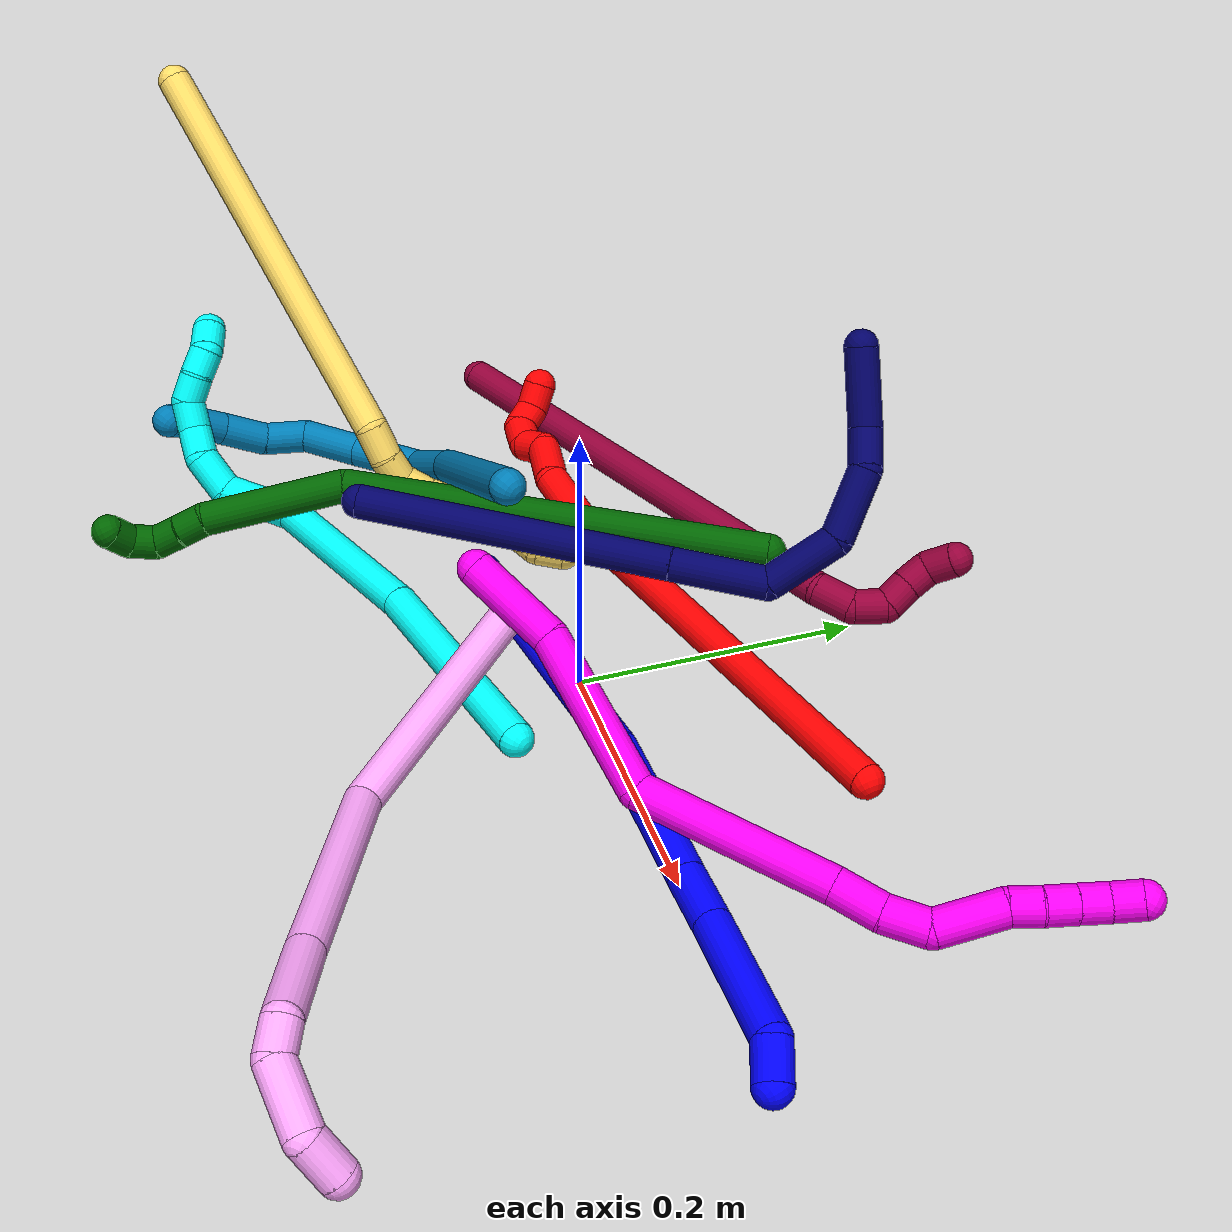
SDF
<sdf version="1.7">
 <world name="default">
  <plugin name="TubeGeneratorPlugin" filename="libtube_generator_plugin.so"/>
  <model name="photoneo_s_sensor">
   <static>1</static>
   <pose>0 0 2 1.57079 1.57079 3.14159</pose>
   <link name="link">
    <inertial><mass>0.1</mass></inertial>
    <sensor name="sensor" type="depth">
     <update_rate>30</update_rate>
     <camera>
      <horizontal_fov>1.22</horizontal_fov>
      <image><width>1920</width><height>1200</height><format>B8G8R8</format></image>
      <clip><near>0.1</near><far>4</far></clip>
      <depth_camera><output>points</output></depth_camera>
     </camera>
     <plugin name="camera_plugin" filename="libgazebo_ros_depth_camera.so">
      <baseline>0.2</baseline>
      <alwaysOn>1</alwaysOn>
      <updateRate>0.0</updateRate>
      <cameraName>camera_ir</cameraName>
      <imageTopicName>/camera/color/image_raw</imageTopicName>
      <cameraInfoTopicName>/camera/color/camera_info</cameraInfoTopicName>
      <depthImageTopicName>/camera/depth/image_raw</depthImageTopicName>
      <depthImageCameraInfoTopicName>/camera/depth/camera_info</depthImageCameraInfoTopicName>
      <pointCloudTopicName>/camera/depth/points</pointCloudTopicName>
      <frameName>fr_optical</frameName>
      <pointCloudCutoff>0.1</pointCloudCutoff>
      <pointCloudCutoffMax>2.0</pointCloudCutoffMax>
      <distortionK1>0</distortionK1>
      <distortionK2>0</distortionK2>
      <distortionK3>0</distortionK3>
      <distortionT1>0</distortionT1>
      <distortionT2>0</distortionT2>
      <CxPrime>0</CxPrime>
      <Cx>0</Cx>
      <Cy>0</Cy>
      <focalLength>0</focalLength>
      <hackBaseline>0</hackBaseline>
     </plugin>
    </sensor>
   </link>
  </model>
  <gravity>0 0 -9.8</gravity>
  <magnetic_field>6e-06 2.3e-05 -4.2e-05</magnetic_field>
  <atmosphere type="adiabatic"/>
  <physics name="default_physics" default="0" type="ode">
   <max_step_size>0.003</max_step_size>
   <real_time_factor>1</real_time_factor>
   <real_time_update_rate>1000</real_time_update_rate>
   <max_contacts>10000</max_contacts>
   <ode>
    <solver>
     <type>quick</type>
     <iters>100</iters>
     <sor>1.3</sor>
     <use_dynamic_moi_rescaling>0</use_dynamic_moi_rescaling>
    </solver>
    <constraints>
     <contact_max_correcting_vel>0</contact_max_correcting_vel>
     <contact_surface_layer>0.001</contact_surface_layer>
     <cfm>0</cfm>
     <erp>0.2</erp>
    </constraints>
   </ode>
  </physics>
  <scene><ambient>0.4 0.4 0.4 1</ambient><background>0.7 0.7 0.7 1</background><shadows>0</shadows></scene>
  <audio><device>default</device></audio>
  <spherical_coordinates>
   <surface_model>EARTH_WGS84</surface_model>
   <latitude_deg>0</latitude_deg>
   <longitude_deg>0</longitude_deg>
   <elevation>0</elevation>
   <heading_deg>0</heading_deg>
  </spherical_coordinates>
  <model name="bin">
   <static>1</static>
   <link name="bottom">
    <collision name="collision-bottom">
     <pose>0 0 -0.01 0 -0 0</pose>
     <geometry><box><size>0.8 0.6 0.02</size></box></geometry>
     <surface>
      <friction><ode><mu>100</mu><mu2>100</mu2></ode></friction>
      <contact><collide_bitmask>65535</collide_bitmask></contact>
     </surface>
    </collision>
   </link>
   <link name="west_wall">
    <collision name="collision-west_wall">
     <pose>-0.41 0 0.1 0 -0 0</pose>
     <geometry><box><size>0.02 0.6 0.2</size></box></geometry>
     <surface>
      <friction><ode><mu>100</mu><mu2>100</mu2></ode></friction>
      <contact><collide_bitmask>65535</collide_bitmask></contact>
     </surface>
    </collision>
   </link>
   <link name="east_wall">
    <collision name="collision-east_wall">
     <pose>0.41 0 0.1 0 -0 0</pose>
     <geometry><box><size>0.02 0.6 0.2</size></box></geometry>
     <surface>
      <friction><ode><mu>100</mu><mu2>100</mu2></ode></friction>
      <contact><collide_bitmask>65535</collide_bitmask></contact>
     </surface>
    </collision>
   </link>
   <link name="south_wall">
    <collision name="collision-south_wall">
     <pose>0 -0.31 0.1 0 -0 0</pose>
     <geometry><box><size>0.8 0.02 0.2</size></box></geometry>
     <surface>
      <friction><ode><mu>100</mu><mu2>100</mu2></ode></friction>
      <contact><collide_bitmask>65535</collide_bitmask></contact>
     </surface>
    </collision>
   </link>
   <link name="north_wall">
    <collision name="collision-north_wall">
     <pose>0 0.31 0.1 0 -0 0</pose>
     <geometry><box><size>0.8 0.02 0.2</size></box></geometry>
     <surface>
      <friction><ode><mu>100</mu><mu2>100</mu2></ode></friction>
      <contact><collide_bitmask>65535</collide_bitmask></contact>
     </surface>
    </collision>
   </link>
  </model>
  <model name="1">
   <static>0</static>
   <link name="1">
    <collision name="collision-cylinder-e_1_1_4">
     <pose>0.097886 0.025939 0.03041 -0.706214 1.18313 -0.485443</pose>
     <geometry><cylinder><radius>0.0125</radius><length>0.211465</length></cylinder></geometry>
     <surface>
      <friction><ode><mu>1.16</mu><mu2>1.16</mu2><slip1>0</slip1><slip2>0</slip2></ode></friction>
      <contact><ode><kp>1e+06</kp><kd>1</kd><max_vel>0</max_vel><min_depth>0.001</min_depth></ode></contact>
     </surface>
    </collision>
    <visual name="visual-cylinder-e_1_1_4">
     <pose>0.097886 0.025939 0.03041 -0.706214 1.18313 -0.485443</pose>
     <geometry><cylinder><radius>0.0125</radius><length>0.211465</length></cylinder></geometry>
     <material><ambient>0 0 1 1</ambient></material>
    </visual>
    <collision name="collision-cylinder-e_2_4_5">
     <pose>0.250681 0.068848 0.087689 -0.563329 1.04612 -0.330661</pose>
     <geometry><cylinder><radius>0.0125</radius><length>0.126883</length></cylinder></geometry>
     <surface>
      <friction><ode><mu>1.16</mu><mu2>1.16</mu2><slip1>0</slip1><slip2>0</slip2></ode></friction>
      <contact><ode><kp>1e+06</kp><kd>1</kd><max_vel>0</max_vel><min_depth>0.001</min_depth></ode></contact>
     </surface>
    </collision>
    <visual name="visual-cylinder-e_2_4_5">
     <pose>0.250681 0.068848 0.087689 -0.563329 1.04612 -0.330661</pose>
     <geometry><cylinder><radius>0.0125</radius><length>0.126883</length></cylinder></geometry>
     <material><ambient>0 0 1 1</ambient></material>
    </visual>
    <collision name="collision-cylinder-e_3_5_6">
     <pose>0.323725 0.091399 0.123114 -0.57799 1.0579 -0.344132</pose>
     <geometry><cylinder><radius>0.0125</radius><length>0.041631</length></cylinder></geometry>
     <surface>
      <friction><ode><mu>1.16</mu><mu2>1.16</mu2><slip1>0</slip1><slip2>0</slip2></ode></friction>
      <contact><ode><kp>1e+06</kp><kd>1</kd><max_vel>0</max_vel><min_depth>0.001</min_depth></ode></contact>
     </surface>
    </collision>
    <visual name="visual-cylinder-e_3_5_6">
     <pose>0.323725 0.091399 0.123114 -0.57799 1.0579 -0.344132</pose>
     <geometry><cylinder><radius>0.0125</radius><length>0.041631</length></cylinder></geometry>
     <material><ambient>0 0 1 1</ambient></material>
    </visual>
    <collision name="collision-cylinder-e_4_6_7">
     <pose>0.381693 0.110365 0.151748 -0.58797 1.02608 -0.337868</pose>
     <geometry><cylinder><radius>0.0125</radius><length>0.093142</length></cylinder></geometry>
     <surface>
      <friction><ode><mu>1.16</mu><mu2>1.16</mu2><slip1>0</slip1><slip2>0</slip2></ode></friction>
      <contact><ode><kp>1e+06</kp><kd>1</kd><max_vel>0</max_vel><min_depth>0.001</min_depth></ode></contact>
     </surface>
    </collision>
    <visual name="visual-cylinder-e_4_6_7">
     <pose>0.381693 0.110365 0.151748 -0.58797 1.02608 -0.337868</pose>
     <geometry><cylinder><radius>0.0125</radius><length>0.093142</length></cylinder></geometry>
     <material><ambient>0 0 1 1</ambient></material>
    </visual>
    <collision name="collision-cylinder-e_5_7_2">
     <pose>0.431173 0.121071 0.180791 0.290436 0.800865 0.123656</pose>
     <geometry><cylinder><radius>0.0125</radius><length>0.02688</length></cylinder></geometry>
     <surface>
      <friction><ode><mu>1.16</mu><mu2>1.16</mu2><slip1>0</slip1><slip2>0</slip2></ode></friction>
      <contact><ode><kp>1e+06</kp><kd>1</kd><max_vel>0</max_vel><min_depth>0.001</min_depth></ode></contact>
     </surface>
    </collision>
    <visual name="visual-cylinder-e_5_7_2">
     <pose>0.431173 0.121071 0.180791 0.290436 0.800865 0.123656</pose>
     <geometry><cylinder><radius>0.0125</radius><length>0.02688</length></cylinder></geometry>
     <material><ambient>0 0 1 1</ambient></material>
    </visual>
    <collision name="collision-sphere-2">
     <pose>0.440822 0.118392 0.189755 0 -0 0</pose>
     <geometry><sphere><radius>0.0125</radius></sphere></geometry>
     <surface>
      <friction><ode><mu>1.16</mu><mu2>1.16</mu2><slip1>0</slip1><slip2>0</slip2></ode></friction>
      <contact><ode><kp>1e+06</kp><kd>1</kd><max_vel>0</max_vel><min_depth>0.001</min_depth></ode></contact>
     </surface>
    </collision>
    <visual name="visual-sphere-2">
     <pose>0.440822 0.118392 0.189755 0 -0 0</pose>
     <geometry><sphere><radius>0.0125</radius></sphere></geometry>
     <material><ambient>0 0 1 1</ambient></material>
    </visual>
    <collision name="collision-sphere-7">
     <pose>0.421524 0.12375 0.171828 0 -0 0</pose>
     <geometry><sphere><radius>0.0125</radius></sphere></geometry>
     <surface>
      <friction><ode><mu>1.16</mu><mu2>1.16</mu2><slip1>0</slip1><slip2>0</slip2></ode></friction>
      <contact><ode><kp>1e+06</kp><kd>1</kd><max_vel>0</max_vel><min_depth>0.001</min_depth></ode></contact>
     </surface>
    </collision>
    <visual name="visual-sphere-7">
     <pose>0.421524 0.12375 0.171828 0 -0 0</pose>
     <geometry><sphere><radius>0.0125</radius></sphere></geometry>
     <material><ambient>0 0 1 1</ambient></material>
    </visual>
    <collision name="collision-sphere-6">
     <pose>0.341862 0.09698 0.131669 0 -0 0</pose>
     <geometry><sphere><radius>0.0125</radius></sphere></geometry>
     <surface>
      <friction><ode><mu>1.16</mu><mu2>1.16</mu2><slip1>0</slip1><slip2>0</slip2></ode></friction>
      <contact><ode><kp>1e+06</kp><kd>1</kd><max_vel>0</max_vel><min_depth>0.001</min_depth></ode></contact>
     </surface>
    </collision>
    <visual name="visual-sphere-6">
     <pose>0.341862 0.09698 0.131669 0 -0 0</pose>
     <geometry><sphere><radius>0.0125</radius></sphere></geometry>
     <material><ambient>0 0 1 1</ambient></material>
    </visual>
    <collision name="collision-sphere-5">
     <pose>0.305588 0.085819 0.114559 0 -0 0</pose>
     <geometry><sphere><radius>0.0125</radius></sphere></geometry>
     <surface>
      <friction><ode><mu>1.16</mu><mu2>1.16</mu2><slip1>0</slip1><slip2>0</slip2></ode></friction>
      <contact><ode><kp>1e+06</kp><kd>1</kd><max_vel>0</max_vel><min_depth>0.001</min_depth></ode></contact>
     </surface>
    </collision>
    <visual name="visual-sphere-5">
     <pose>0.305588 0.085819 0.114559 0 -0 0</pose>
     <geometry><sphere><radius>0.0125</radius></sphere></geometry>
     <material><ambient>0 0 1 1</ambient></material>
    </visual>
    <collision name="collision-sphere-1">
     <geometry><sphere><radius>0.0125</radius></sphere></geometry>
     <surface>
      <friction><ode><mu>1.16</mu><mu2>1.16</mu2><slip1>0</slip1><slip2>0</slip2></ode></friction>
      <contact><ode><kp>1e+06</kp><kd>1</kd><max_vel>0</max_vel><min_depth>0.001</min_depth></ode></contact>
     </surface>
    </collision>
    <visual name="visual-sphere-1">
     <geometry><sphere><radius>0.0125</radius></sphere></geometry>
     <material><ambient>0 0 1 1</ambient></material>
    </visual>
    <collision name="collision-sphere-4">
     <pose>0.195773 0.051878 0.06082 0 -0 0</pose>
     <geometry><sphere><radius>0.0125</radius></sphere></geometry>
     <surface>
      <friction><ode><mu>1.16</mu><mu2>1.16</mu2><slip1>0</slip1><slip2>0</slip2></ode></friction>
      <contact><ode><kp>1e+06</kp><kd>1</kd><max_vel>0</max_vel><min_depth>0.001</min_depth></ode></contact>
     </surface>
    </collision>
    <visual name="visual-sphere-4">
     <pose>0.195773 0.051878 0.06082 0 -0 0</pose>
     <geometry><sphere><radius>0.0125</radius></sphere></geometry>
     <material><ambient>0 0 1 1</ambient></material>
    </visual>
    <inertial>
     <pose>0.22625 0.06312 0.083352 0 -0 0</pose>
     <mass>0.5</mass>
     <inertia>
      <ixx>0.000242</ixx>
      <ixy>0</ixy>
      <ixz>0</ixz>
      <iyy>0.000829</iyy>
      <iyz>0</iyz>
      <izz>-0.001207</izz>
     </inertia>
    </inertial>
   </link>
   <pose>-0.125701 -0.032196 0.012259 1.63876 0.236014 0.462138</pose>
  </model>
  <model name="2">
   <static>0</static>
   <link name="2">
    <collision name="collision-cylinder-e_1_1_4">
     <pose>-0.08597 -0.002961 0.142561 0.020765 -0.542554 -0.005776</pose>
     <geometry><cylinder><radius>0.0125</radius><length>0.333006</length></cylinder></geometry>
     <surface>
      <friction><ode><mu>1.16</mu><mu2>1.16</mu2><slip1>0</slip1><slip2>0</slip2></ode></friction>
      <contact><ode><kp>1e+06</kp><kd>1</kd><max_vel>0</max_vel><min_depth>0.001</min_depth></ode></contact>
     </surface>
    </collision>
    <visual name="visual-cylinder-e_1_1_4">
     <pose>-0.08597 -0.002961 0.142561 0.020765 -0.542554 -0.005776</pose>
     <geometry><cylinder><radius>0.0125</radius><length>0.333006</length></cylinder></geometry>
     <material><ambient>1 0 0 1</ambient></material>
    </visual>
    <collision name="collision-cylinder-e_2_4_5">
     <pose>-0.178803 -0.006488 0.30804 0.024716 -0.290923 -0.003621</pose>
     <geometry><cylinder><radius>0.0125</radius><length>0.047859</length></cylinder></geometry>
     <surface>
      <friction><ode><mu>1.16</mu><mu2>1.16</mu2><slip1>0</slip1><slip2>0</slip2></ode></friction>
      <contact><ode><kp>1e+06</kp><kd>1</kd><max_vel>0</max_vel><min_depth>0.001</min_depth></ode></contact>
     </surface>
    </collision>
    <visual name="visual-cylinder-e_2_4_5">
     <pose>-0.178803 -0.006488 0.30804 0.024716 -0.290923 -0.003621</pose>
     <geometry><cylinder><radius>0.0125</radius><length>0.047859</length></cylinder></geometry>
     <material><ambient>1 0 0 1</ambient></material>
    </visual>
    <collision name="collision-cylinder-e_3_5_6">
     <pose>-0.192619 -0.000263 0.347358 -0.392575 -0.373251 0.075059</pose>
     <geometry><cylinder><radius>0.0125</radius><length>0.038129</length></cylinder></geometry>
     <surface>
      <friction><ode><mu>1.16</mu><mu2>1.16</mu2><slip1>0</slip1><slip2>0</slip2></ode></friction>
      <contact><ode><kp>1e+06</kp><kd>1</kd><max_vel>0</max_vel><min_depth>0.001</min_depth></ode></contact>
     </surface>
    </collision>
    <visual name="visual-cylinder-e_3_5_6">
     <pose>-0.192619 -0.000263 0.347358 -0.392575 -0.373251 0.075059</pose>
     <geometry><cylinder><radius>0.0125</radius><length>0.038129</length></cylinder></geometry>
     <material><ambient>1 0 0 1</ambient></material>
    </visual>
    <collision name="collision-cylinder-e_4_6_7">
     <pose>-0.207221 0.004468 0.370305 0.304868 -0.839622 -0.136926</pose>
     <geometry><cylinder><radius>0.0125</radius><length>0.020554</length></cylinder></geometry>
     <surface>
      <friction><ode><mu>1.16</mu><mu2>1.16</mu2><slip1>0</slip1><slip2>0</slip2></ode></friction>
      <contact><ode><kp>1e+06</kp><kd>1</kd><max_vel>0</max_vel><min_depth>0.001</min_depth></ode></contact>
     </surface>
    </collision>
    <visual name="visual-cylinder-e_4_6_7">
     <pose>-0.207221 0.004468 0.370305 0.304868 -0.839622 -0.136926</pose>
     <geometry><cylinder><radius>0.0125</radius><length>0.020554</length></cylinder></geometry>
     <material><ambient>1 0 0 1</ambient></material>
    </visual>
    <collision name="collision-cylinder-e_5_7_8">
     <pose>-0.217759 0.005194 0.386165 -0.290572 -0.288807 0.042547</pose>
     <geometry><cylinder><radius>0.0125</radius><length>0.020283</length></cylinder></geometry>
     <surface>
      <friction><ode><mu>1.16</mu><mu2>1.16</mu2><slip1>0</slip1><slip2>0</slip2></ode></friction>
      <contact><ode><kp>1e+06</kp><kd>1</kd><max_vel>0</max_vel><min_depth>0.001</min_depth></ode></contact>
     </surface>
    </collision>
    <visual name="visual-cylinder-e_5_7_8">
     <pose>-0.217759 0.005194 0.386165 -0.290572 -0.288807 0.042547</pose>
     <geometry><cylinder><radius>0.0125</radius><length>0.020283</length></cylinder></geometry>
     <material><ambient>1 0 0 1</ambient></material>
    </visual>
    <collision name="collision-cylinder-e_6_8_9">
     <pose>-0.219443 0.01565 0.40181 -0.880827 0.120481 -0.056835</pose>
     <geometry><cylinder><radius>0.0125</radius><length>0.020037</length></cylinder></geometry>
     <surface>
      <friction><ode><mu>1.16</mu><mu2>1.16</mu2><slip1>0</slip1><slip2>0</slip2></ode></friction>
      <contact><ode><kp>1e+06</kp><kd>1</kd><max_vel>0</max_vel><min_depth>0.001</min_depth></ode></contact>
     </surface>
    </collision>
    <visual name="visual-cylinder-e_6_8_9">
     <pose>-0.219443 0.01565 0.40181 -0.880827 0.120481 -0.056835</pose>
     <geometry><cylinder><radius>0.0125</radius><length>0.020037</length></cylinder></geometry>
     <material><ambient>1 0 0 1</ambient></material>
    </visual>
    <collision name="collision-cylinder-e_7_9_2">
     <pose>-0.212252 0.027376 0.415142 -0.524962 0.637064 -0.176739</pose>
     <geometry><cylinder><radius>0.0125</radius><length>0.020132</length></cylinder></geometry>
     <surface>
      <friction><ode><mu>1.16</mu><mu2>1.16</mu2><slip1>0</slip1><slip2>0</slip2></ode></friction>
      <contact><ode><kp>1e+06</kp><kd>1</kd><max_vel>0</max_vel><min_depth>0.001</min_depth></ode></contact>
     </surface>
    </collision>
    <visual name="visual-cylinder-e_7_9_2">
     <pose>-0.212252 0.027376 0.415142 -0.524962 0.637064 -0.176739</pose>
     <geometry><cylinder><radius>0.0125</radius><length>0.020132</length></cylinder></geometry>
     <material><ambient>1 0 0 1</ambient></material>
    </visual>
    <collision name="collision-sphere-2">
     <pose>-0.206264 0.031432 0.422144 0 -0 0</pose>
     <geometry><sphere><radius>0.0125</radius></sphere></geometry>
     <surface>
      <friction><ode><mu>1.16</mu><mu2>1.16</mu2><slip1>0</slip1><slip2>0</slip2></ode></friction>
      <contact><ode><kp>1e+06</kp><kd>1</kd><max_vel>0</max_vel><min_depth>0.001</min_depth></ode></contact>
     </surface>
    </collision>
    <visual name="visual-sphere-2">
     <pose>-0.206264 0.031432 0.422144 0 -0 0</pose>
     <geometry><sphere><radius>0.0125</radius></sphere></geometry>
     <material><ambient>1 0 0 1</ambient></material>
    </visual>
    <collision name="collision-sphere-9">
     <pose>-0.218239 0.023321 0.408141 0 -0 0</pose>
     <geometry><sphere><radius>0.0125</radius></sphere></geometry>
     <surface>
      <friction><ode><mu>1.16</mu><mu2>1.16</mu2><slip1>0</slip1><slip2>0</slip2></ode></friction>
      <contact><ode><kp>1e+06</kp><kd>1</kd><max_vel>0</max_vel><min_depth>0.001</min_depth></ode></contact>
     </surface>
    </collision>
    <visual name="visual-sphere-9">
     <pose>-0.218239 0.023321 0.408141 0 -0 0</pose>
     <geometry><sphere><radius>0.0125</radius></sphere></geometry>
     <material><ambient>1 0 0 1</ambient></material>
    </visual>
    <collision name="collision-sphere-4">
     <pose>-0.17194 -0.005921 0.285123 0 -0 0</pose>
     <geometry><sphere><radius>0.0125</radius></sphere></geometry>
     <surface>
      <friction><ode><mu>1.16</mu><mu2>1.16</mu2><slip1>0</slip1><slip2>0</slip2></ode></friction>
      <contact><ode><kp>1e+06</kp><kd>1</kd><max_vel>0</max_vel><min_depth>0.001</min_depth></ode></contact>
     </surface>
    </collision>
    <visual name="visual-sphere-4">
     <pose>-0.17194 -0.005921 0.285123 0 -0 0</pose>
     <geometry><sphere><radius>0.0125</radius></sphere></geometry>
     <material><ambient>1 0 0 1</ambient></material>
    </visual>
    <collision name="collision-sphere-1">
     <geometry><sphere><radius>0.0125</radius></sphere></geometry>
     <surface>
      <friction><ode><mu>1.16</mu><mu2>1.16</mu2><slip1>0</slip1><slip2>0</slip2></ode></friction>
      <contact><ode><kp>1e+06</kp><kd>1</kd><max_vel>0</max_vel><min_depth>0.001</min_depth></ode></contact>
     </surface>
    </collision>
    <visual name="visual-sphere-1">
     <geometry><sphere><radius>0.0125</radius></sphere></geometry>
     <material><ambient>1 0 0 1</ambient></material>
    </visual>
    <collision name="collision-sphere-8">
     <pose>-0.220648 0.007979 0.395479 0 -0 0</pose>
     <geometry><sphere><radius>0.0125</radius></sphere></geometry>
     <surface>
      <friction><ode><mu>1.16</mu><mu2>1.16</mu2><slip1>0</slip1><slip2>0</slip2></ode></friction>
      <contact><ode><kp>1e+06</kp><kd>1</kd><max_vel>0</max_vel><min_depth>0.001</min_depth></ode></contact>
     </surface>
    </collision>
    <visual name="visual-sphere-8">
     <pose>-0.220648 0.007979 0.395479 0 -0 0</pose>
     <geometry><sphere><radius>0.0125</radius></sphere></geometry>
     <material><ambient>1 0 0 1</ambient></material>
    </visual>
    <collision name="collision-sphere-5">
     <pose>-0.185667 -0.007054 0.330956 0 -0 0</pose>
     <geometry><sphere><radius>0.0125</radius></sphere></geometry>
     <surface>
      <friction><ode><mu>1.16</mu><mu2>1.16</mu2><slip1>0</slip1><slip2>0</slip2></ode></friction>
      <contact><ode><kp>1e+06</kp><kd>1</kd><max_vel>0</max_vel><min_depth>0.001</min_depth></ode></contact>
     </surface>
    </collision>
    <visual name="visual-sphere-5">
     <pose>-0.185667 -0.007054 0.330956 0 -0 0</pose>
     <geometry><sphere><radius>0.0125</radius></sphere></geometry>
     <material><ambient>1 0 0 1</ambient></material>
    </visual>
    <collision name="collision-sphere-6">
     <pose>-0.199571 0.006528 0.363759 0 -0 0</pose>
     <geometry><sphere><radius>0.0125</radius></sphere></geometry>
     <surface>
      <friction><ode><mu>1.16</mu><mu2>1.16</mu2><slip1>0</slip1><slip2>0</slip2></ode></friction>
      <contact><ode><kp>1e+06</kp><kd>1</kd><max_vel>0</max_vel><min_depth>0.001</min_depth></ode></contact>
     </surface>
    </collision>
    <visual name="visual-sphere-6">
     <pose>-0.199571 0.006528 0.363759 0 -0 0</pose>
     <geometry><sphere><radius>0.0125</radius></sphere></geometry>
     <material><ambient>1 0 0 1</ambient></material>
    </visual>
    <collision name="collision-sphere-7">
     <pose>-0.214871 0.002408 0.376851 0 -0 0</pose>
     <geometry><sphere><radius>0.0125</radius></sphere></geometry>
     <surface>
      <friction><ode><mu>1.16</mu><mu2>1.16</mu2><slip1>0</slip1><slip2>0</slip2></ode></friction>
      <contact><ode><kp>1e+06</kp><kd>1</kd><max_vel>0</max_vel><min_depth>0.001</min_depth></ode></contact>
     </surface>
    </collision>
    <visual name="visual-sphere-7">
     <pose>-0.214871 0.002408 0.376851 0 -0 0</pose>
     <geometry><sphere><radius>0.0125</radius></sphere></geometry>
     <material><ambient>1 0 0 1</ambient></material>
    </visual>
    <inertial>
     <pose>-0.123752 -0.000489 0.214626 0 -0 0</pose>
     <mass>0.5</mass>
     <inertia>
      <ixx>0.002636</ixx>
      <ixy>0</ixy>
      <ixz>0</ixz>
      <iyy>0.003099</iyy>
      <iyz>0</iyz>
      <izz>0.001686</izz>
     </inertia>
    </inertial>
   </link>
   <pose>0.160036 0.14107 0.01186 -0.322479 -1.00872 0.520316</pose>
  </model>
  <model name="3">
   <static>0</static>
   <link name="3">
    <collision name="collision-cylinder-e_1_1_4">
     <pose>-0.014549 -0.007096 0.08056 0.08786 -0.177996 -0.007845</pose>
     <geometry><cylinder><radius>0.0125</radius><length>0.16434</length></cylinder></geometry>
     <surface>
      <friction><ode><mu>1.16</mu><mu2>1.16</mu2><slip1>0</slip1><slip2>0</slip2></ode></friction>
      <contact><ode><kp>1e+06</kp><kd>1</kd><max_vel>0</max_vel><min_depth>0.001</min_depth></ode></contact>
     </surface>
    </collision>
    <visual name="visual-cylinder-e_1_1_4">
     <pose>-0.014549 -0.007096 0.08056 0.08786 -0.177996 -0.007845</pose>
     <geometry><cylinder><radius>0.0125</radius><length>0.16434</length></cylinder></geometry>
     <material><ambient>0.003922 1 0.996078 1</ambient></material>
    </visual>
    <collision name="collision-cylinder-e_2_4_5">
     <pose>-0.032626 -0.018945 0.232584 0.066409 -0.049224 -0.001635</pose>
     <geometry><cylinder><radius>0.0125</radius><length>0.143418</length></cylinder></geometry>
     <surface>
      <friction><ode><mu>1.16</mu><mu2>1.16</mu2><slip1>0</slip1><slip2>0</slip2></ode></friction>
      <contact><ode><kp>1e+06</kp><kd>1</kd><max_vel>0</max_vel><min_depth>0.001</min_depth></ode></contact>
     </surface>
    </collision>
    <visual name="visual-cylinder-e_2_4_5">
     <pose>-0.032626 -0.018945 0.232584 0.066409 -0.049224 -0.001635</pose>
     <geometry><cylinder><radius>0.0125</radius><length>0.143418</length></cylinder></geometry>
     <material><ambient>0.003922 1 0.996078 1</ambient></material>
    </visual>
    <collision name="collision-cylinder-e_3_5_6">
     <pose>-0.026898 -0.012941 0.326605 -0.445 0.354713 -0.08106</pose>
     <geometry><cylinder><radius>0.0125</radius><length>0.053299</length></cylinder></geometry>
     <surface>
      <friction><ode><mu>1.16</mu><mu2>1.16</mu2><slip1>0</slip1><slip2>0</slip2></ode></friction>
      <contact><ode><kp>1e+06</kp><kd>1</kd><max_vel>0</max_vel><min_depth>0.001</min_depth></ode></contact>
     </surface>
    </collision>
    <visual name="visual-cylinder-e_3_5_6">
     <pose>-0.026898 -0.012941 0.326605 -0.445 0.354713 -0.08106</pose>
     <geometry><cylinder><radius>0.0125</radius><length>0.053299</length></cylinder></geometry>
     <material><ambient>0.003922 1 0.996078 1</ambient></material>
    </visual>
    <collision name="collision-cylinder-e_4_6_7">
     <pose>-0.020656 0.007183 0.360978 -0.670259 -0.197256 0.068894</pose>
     <geometry><cylinder><radius>0.0125</radius><length>0.030753</length></cylinder></geometry>
     <surface>
      <friction><ode><mu>1.16</mu><mu2>1.16</mu2><slip1>0</slip1><slip2>0</slip2></ode></friction>
      <contact><ode><kp>1e+06</kp><kd>1</kd><max_vel>0</max_vel><min_depth>0.001</min_depth></ode></contact>
     </surface>
    </collision>
    <visual name="visual-cylinder-e_4_6_7">
     <pose>-0.020656 0.007183 0.360978 -0.670259 -0.197256 0.068894</pose>
     <geometry><cylinder><radius>0.0125</radius><length>0.030753</length></cylinder></geometry>
     <material><ambient>0.003922 1 0.996078 1</ambient></material>
    </visual>
    <collision name="collision-cylinder-e_5_7_8">
     <pose>-0.030211 0.020069 0.382076 -0.362444 -0.582693 0.109785</pose>
     <geometry><cylinder><radius>0.0125</radius><length>0.023777</length></cylinder></geometry>
     <surface>
      <friction><ode><mu>1.16</mu><mu2>1.16</mu2><slip1>0</slip1><slip2>0</slip2></ode></friction>
      <contact><ode><kp>1e+06</kp><kd>1</kd><max_vel>0</max_vel><min_depth>0.001</min_depth></ode></contact>
     </surface>
    </collision>
    <visual name="visual-cylinder-e_5_7_8">
     <pose>-0.030211 0.020069 0.382076 -0.362444 -0.582693 0.109785</pose>
     <geometry><cylinder><radius>0.0125</radius><length>0.023777</length></cylinder></geometry>
     <material><ambient>0.003922 1 0.996078 1</ambient></material>
    </visual>
    <collision name="collision-cylinder-e_6_8_9">
     <pose>-0.043046 0.03055 0.397513 -0.846794 -0.5952 0.274698</pose>
     <geometry><cylinder><radius>0.0125</radius><length>0.022445</length></cylinder></geometry>
     <surface>
      <friction><ode><mu>1.16</mu><mu2>1.16</mu2><slip1>0</slip1><slip2>0</slip2></ode></friction>
      <contact><ode><kp>1e+06</kp><kd>1</kd><max_vel>0</max_vel><min_depth>0.001</min_depth></ode></contact>
     </surface>
    </collision>
    <visual name="visual-cylinder-e_6_8_9">
     <pose>-0.043046 0.03055 0.397513 -0.846794 -0.5952 0.274698</pose>
     <geometry><cylinder><radius>0.0125</radius><length>0.022445</length></cylinder></geometry>
     <material><ambient>0.003922 1 0.996078 1</ambient></material>
    </visual>
    <collision name="collision-cylinder-e_7_9_10">
     <pose>-0.058362 0.04221 0.404789 -1.3365 -1.0794 0.883431</pose>
     <geometry><cylinder><radius>0.0125</radius><length>0.020471</length></cylinder></geometry>
     <surface>
      <friction><ode><mu>1.16</mu><mu2>1.16</mu2><slip1>0</slip1><slip2>0</slip2></ode></friction>
      <contact><ode><kp>1e+06</kp><kd>1</kd><max_vel>0</max_vel><min_depth>0.001</min_depth></ode></contact>
     </surface>
    </collision>
    <visual name="visual-cylinder-e_7_9_10">
     <pose>-0.058362 0.04221 0.404789 -1.3365 -1.0794 0.883431</pose>
     <geometry><cylinder><radius>0.0125</radius><length>0.020471</length></cylinder></geometry>
     <material><ambient>0.003922 1 0.996078 1</ambient></material>
    </visual>
    <collision name="collision-cylinder-e_8_10_11">
     <pose>-0.076729 0.04982 0.408074 -0.931902 -1.20037 0.662959</pose>
     <geometry><cylinder><radius>0.0125</radius><length>0.020045</length></cylinder></geometry>
     <surface>
      <friction><ode><mu>1.16</mu><mu2>1.16</mu2><slip1>0</slip1><slip2>0</slip2></ode></friction>
      <contact><ode><kp>1e+06</kp><kd>1</kd><max_vel>0</max_vel><min_depth>0.001</min_depth></ode></contact>
     </surface>
    </collision>
    <visual name="visual-cylinder-e_8_10_11">
     <pose>-0.076729 0.04982 0.408074 -0.931902 -1.20037 0.662959</pose>
     <geometry><cylinder><radius>0.0125</radius><length>0.020045</length></cylinder></geometry>
     <material><ambient>0.003922 1 0.996078 1</ambient></material>
    </visual>
    <collision name="collision-cylinder-e_9_11_2">
     <pose>-0.093725 0.05228 0.41774 0.060165 -0.794404 -0.025245</pose>
     <geometry><cylinder><radius>0.0125</radius><length>0.021452</length></cylinder></geometry>
     <surface>
      <friction><ode><mu>1.16</mu><mu2>1.16</mu2><slip1>0</slip1><slip2>0</slip2></ode></friction>
      <contact><ode><kp>1e+06</kp><kd>1</kd><max_vel>0</max_vel><min_depth>0.001</min_depth></ode></contact>
     </surface>
    </collision>
    <visual name="visual-cylinder-e_9_11_2">
     <pose>-0.093725 0.05228 0.41774 0.060165 -0.794404 -0.025245</pose>
     <geometry><cylinder><radius>0.0125</radius><length>0.021452</length></cylinder></geometry>
     <material><ambient>0.003922 1 0.996078 1</ambient></material>
    </visual>
    <collision name="collision-sphere-2">
     <pose>-0.101377 0.051829 0.425242 0 -0 0</pose>
     <geometry><sphere><radius>0.0125</radius></sphere></geometry>
     <surface>
      <friction><ode><mu>1.16</mu><mu2>1.16</mu2><slip1>0</slip1><slip2>0</slip2></ode></friction>
      <contact><ode><kp>1e+06</kp><kd>1</kd><max_vel>0</max_vel><min_depth>0.001</min_depth></ode></contact>
     </surface>
    </collision>
    <visual name="visual-sphere-2">
     <pose>-0.101377 0.051829 0.425242 0 -0 0</pose>
     <geometry><sphere><radius>0.0125</radius></sphere></geometry>
     <material><ambient>0.003922 1 0.996078 1</ambient></material>
    </visual>
    <collision name="collision-sphere-11">
     <pose>-0.086072 0.052732 0.410238 0 -0 0</pose>
     <geometry><sphere><radius>0.0125</radius></sphere></geometry>
     <surface>
      <friction><ode><mu>1.16</mu><mu2>1.16</mu2><slip1>0</slip1><slip2>0</slip2></ode></friction>
      <contact><ode><kp>1e+06</kp><kd>1</kd><max_vel>0</max_vel><min_depth>0.001</min_depth></ode></contact>
     </surface>
    </collision>
    <visual name="visual-sphere-11">
     <pose>-0.086072 0.052732 0.410238 0 -0 0</pose>
     <geometry><sphere><radius>0.0125</radius></sphere></geometry>
     <material><ambient>0.003922 1 0.996078 1</ambient></material>
    </visual>
    <collision name="collision-sphere-10">
     <pose>-0.067387 0.046907 0.405911 0 -0 0</pose>
     <geometry><sphere><radius>0.0125</radius></sphere></geometry>
     <surface>
      <friction><ode><mu>1.16</mu><mu2>1.16</mu2><slip1>0</slip1><slip2>0</slip2></ode></friction>
      <contact><ode><kp>1e+06</kp><kd>1</kd><max_vel>0</max_vel><min_depth>0.001</min_depth></ode></contact>
     </surface>
    </collision>
    <visual name="visual-sphere-10">
     <pose>-0.067387 0.046907 0.405911 0 -0 0</pose>
     <geometry><sphere><radius>0.0125</radius></sphere></geometry>
     <material><ambient>0.003922 1 0.996078 1</ambient></material>
    </visual>
    <collision name="collision-sphere-9">
     <pose>-0.049338 0.037512 0.403668 0 -0 0</pose>
     <geometry><sphere><radius>0.0125</radius></sphere></geometry>
     <surface>
      <friction><ode><mu>1.16</mu><mu2>1.16</mu2><slip1>0</slip1><slip2>0</slip2></ode></friction>
      <contact><ode><kp>1e+06</kp><kd>1</kd><max_vel>0</max_vel><min_depth>0.001</min_depth></ode></contact>
     </surface>
    </collision>
    <visual name="visual-sphere-9">
     <pose>-0.049338 0.037512 0.403668 0 -0 0</pose>
     <geometry><sphere><radius>0.0125</radius></sphere></geometry>
     <material><ambient>0.003922 1 0.996078 1</ambient></material>
    </visual>
    <collision name="collision-sphere-4">
     <pose>-0.029098 -0.014193 0.16112 0 -0 0</pose>
     <geometry><sphere><radius>0.0125</radius></sphere></geometry>
     <surface>
      <friction><ode><mu>1.16</mu><mu2>1.16</mu2><slip1>0</slip1><slip2>0</slip2></ode></friction>
      <contact><ode><kp>1e+06</kp><kd>1</kd><max_vel>0</max_vel><min_depth>0.001</min_depth></ode></contact>
     </surface>
    </collision>
    <visual name="visual-sphere-4">
     <pose>-0.029098 -0.014193 0.16112 0 -0 0</pose>
     <geometry><sphere><radius>0.0125</radius></sphere></geometry>
     <material><ambient>0.003922 1 0.996078 1</ambient></material>
    </visual>
    <collision name="collision-sphere-1">
     <geometry><sphere><radius>0.0125</radius></sphere></geometry>
     <surface>
      <friction><ode><mu>1.16</mu><mu2>1.16</mu2><slip1>0</slip1><slip2>0</slip2></ode></friction>
      <contact><ode><kp>1e+06</kp><kd>1</kd><max_vel>0</max_vel><min_depth>0.001</min_depth></ode></contact>
     </surface>
    </collision>
    <visual name="visual-sphere-1">
     <geometry><sphere><radius>0.0125</radius></sphere></geometry>
     <material><ambient>0.003922 1 0.996078 1</ambient></material>
    </visual>
    <collision name="collision-sphere-8">
     <pose>-0.036753 0.023588 0.391357 0 -0 0</pose>
     <geometry><sphere><radius>0.0125</radius></sphere></geometry>
     <surface>
      <friction><ode><mu>1.16</mu><mu2>1.16</mu2><slip1>0</slip1><slip2>0</slip2></ode></friction>
      <contact><ode><kp>1e+06</kp><kd>1</kd><max_vel>0</max_vel><min_depth>0.001</min_depth></ode></contact>
     </surface>
    </collision>
    <visual name="visual-sphere-8">
     <pose>-0.036753 0.023588 0.391357 0 -0 0</pose>
     <geometry><sphere><radius>0.0125</radius></sphere></geometry>
     <material><ambient>0.003922 1 0.996078 1</ambient></material>
    </visual>
    <collision name="collision-sphere-5">
     <pose>-0.036154 -0.023698 0.304048 0 -0 0</pose>
     <geometry><sphere><radius>0.0125</radius></sphere></geometry>
     <surface>
      <friction><ode><mu>1.16</mu><mu2>1.16</mu2><slip1>0</slip1><slip2>0</slip2></ode></friction>
      <contact><ode><kp>1e+06</kp><kd>1</kd><max_vel>0</max_vel><min_depth>0.001</min_depth></ode></contact>
     </surface>
    </collision>
    <visual name="visual-sphere-5">
     <pose>-0.036154 -0.023698 0.304048 0 -0 0</pose>
     <geometry><sphere><radius>0.0125</radius></sphere></geometry>
     <material><ambient>0.003922 1 0.996078 1</ambient></material>
    </visual>
    <collision name="collision-sphere-6">
     <pose>-0.017643 -0.002184 0.349161 0 -0 0</pose>
     <geometry><sphere><radius>0.0125</radius></sphere></geometry>
     <surface>
      <friction><ode><mu>1.16</mu><mu2>1.16</mu2><slip1>0</slip1><slip2>0</slip2></ode></friction>
      <contact><ode><kp>1e+06</kp><kd>1</kd><max_vel>0</max_vel><min_depth>0.001</min_depth></ode></contact>
     </surface>
    </collision>
    <visual name="visual-sphere-6">
     <pose>-0.017643 -0.002184 0.349161 0 -0 0</pose>
     <geometry><sphere><radius>0.0125</radius></sphere></geometry>
     <material><ambient>0.003922 1 0.996078 1</ambient></material>
    </visual>
    <collision name="collision-sphere-7">
     <pose>-0.02367 0.016549 0.372794 0 -0 0</pose>
     <geometry><sphere><radius>0.0125</radius></sphere></geometry>
     <surface>
      <friction><ode><mu>1.16</mu><mu2>1.16</mu2><slip1>0</slip1><slip2>0</slip2></ode></friction>
      <contact><ode><kp>1e+06</kp><kd>1</kd><max_vel>0</max_vel><min_depth>0.001</min_depth></ode></contact>
     </surface>
    </collision>
    <visual name="visual-sphere-7">
     <pose>-0.02367 0.016549 0.372794 0 -0 0</pose>
     <geometry><sphere><radius>0.0125</radius></sphere></geometry>
     <material><ambient>0.003922 1 0.996078 1</ambient></material>
    </visual>
    <inertial>
     <pose>-0.031134 -0.00041 0.237078 0 -0 0</pose>
     <mass>0.5</mass>
     <inertia>
      <ixx>0.000633</ixx>
      <ixy>0</ixy>
      <ixz>0</ixz>
      <iyy>0.000651</iyy>
      <iyz>0</iyz>
      <izz>0.000152</izz>
     </inertia>
    </inertial>
   </link>
   <pose>0.054867 -0.06134 0.012221 1.56085 0.502055 -1.13867</pose>
  </model>
  <model name="4">
   <static>0</static>
   <link name="4">
    <collision name="collision-cylinder-e_1_1_4">
     <pose>0.009214 0.01263 0.089012 -0.140946 0.102132 -0.007216</pose>
     <geometry><cylinder><radius>0.0125</radius><length>0.180749</length></cylinder></geometry>
     <surface>
      <friction><ode><mu>1.16</mu><mu2>1.16</mu2><slip1>0</slip1><slip2>0</slip2></ode></friction>
      <contact><ode><kp>1e+06</kp><kd>1</kd><max_vel>0</max_vel><min_depth>0.001</min_depth></ode></contact>
     </surface>
    </collision>
    <visual name="visual-cylinder-e_1_1_4">
     <pose>0.009214 0.01263 0.089012 -0.140946 0.102132 -0.007216</pose>
     <geometry><cylinder><radius>0.0125</radius><length>0.180749</length></cylinder></geometry>
     <material><ambient>1 0.65098 0.996078 1</ambient></material>
    </visual>
    <collision name="collision-cylinder-e_2_4_5">
     <pose>0.023633 -0.008778 0.249012 0.447096 0.066019 0.015015</pose>
     <geometry><cylinder><radius>0.0125</radius><length>0.157797</length></cylinder></geometry>
     <surface>
      <friction><ode><mu>1.16</mu><mu2>1.16</mu2><slip1>0</slip1><slip2>0</slip2></ode></friction>
      <contact><ode><kp>1e+06</kp><kd>1</kd><max_vel>0</max_vel><min_depth>0.001</min_depth></ode></contact>
     </surface>
    </collision>
    <visual name="visual-cylinder-e_2_4_5">
     <pose>0.023633 -0.008778 0.249012 0.447096 0.066019 0.015015</pose>
     <geometry><cylinder><radius>0.0125</radius><length>0.157797</length></cylinder></geometry>
     <material><ambient>1 0.65098 0.996078 1</ambient></material>
    </visual>
    <collision name="collision-cylinder-e_3_5_6">
     <pose>0.031493 -0.059762 0.348382 0.538266 0.080153 0.022119</pose>
     <geometry><cylinder><radius>0.0125</radius><length>0.066326</length></cylinder></geometry>
     <surface>
      <friction><ode><mu>1.16</mu><mu2>1.16</mu2><slip1>0</slip1><slip2>0</slip2></ode></friction>
      <contact><ode><kp>1e+06</kp><kd>1</kd><max_vel>0</max_vel><min_depth>0.001</min_depth></ode></contact>
     </surface>
    </collision>
    <visual name="visual-cylinder-e_3_5_6">
     <pose>0.031493 -0.059762 0.348382 0.538266 0.080153 0.022119</pose>
     <geometry><cylinder><radius>0.0125</radius><length>0.066326</length></cylinder></geometry>
     <material><ambient>1 0.65098 0.996078 1</ambient></material>
    </visual>
    <collision name="collision-cylinder-e_4_6_7">
     <pose>0.030962 -0.076972 0.387328 0.024971 -0.292936 -0.003684</pose>
     <geometry><cylinder><radius>0.0125</radius><length>0.022074</length></cylinder></geometry>
     <surface>
      <friction><ode><mu>1.16</mu><mu2>1.16</mu2><slip1>0</slip1><slip2>0</slip2></ode></friction>
      <contact><ode><kp>1e+06</kp><kd>1</kd><max_vel>0</max_vel><min_depth>0.001</min_depth></ode></contact>
     </surface>
    </collision>
    <visual name="visual-cylinder-e_4_6_7">
     <pose>0.030962 -0.076972 0.387328 0.024971 -0.292936 -0.003684</pose>
     <geometry><cylinder><radius>0.0125</radius><length>0.022074</length></cylinder></geometry>
     <material><ambient>1 0.65098 0.996078 1</ambient></material>
    </visual>
    <collision name="collision-cylinder-e_5_7_8">
     <pose>0.012245 -0.083254 0.412739 0.385076 -0.769823 -0.157631</pose>
     <geometry><cylinder><radius>0.0125</radius><length>0.044625</length></cylinder></geometry>
     <surface>
      <friction><ode><mu>1.16</mu><mu2>1.16</mu2><slip1>0</slip1><slip2>0</slip2></ode></friction>
      <contact><ode><kp>1e+06</kp><kd>1</kd><max_vel>0</max_vel><min_depth>0.001</min_depth></ode></contact>
     </surface>
    </collision>
    <visual name="visual-cylinder-e_5_7_8">
     <pose>0.012245 -0.083254 0.412739 0.385076 -0.769823 -0.157631</pose>
     <geometry><cylinder><radius>0.0125</radius><length>0.044625</length></cylinder></geometry>
     <material><ambient>1 0.65098 0.996078 1</ambient></material>
    </visual>
    <collision name="collision-cylinder-e_6_8_2">
     <pose>-0.01728 -0.08813 0.429798 -0.476736 -1.39486 0.401709</pose>
     <geometry><cylinder><radius>0.0125</radius><length>0.02843</length></cylinder></geometry>
     <surface>
      <friction><ode><mu>1.16</mu><mu2>1.16</mu2><slip1>0</slip1><slip2>0</slip2></ode></friction>
      <contact><ode><kp>1e+06</kp><kd>1</kd><max_vel>0</max_vel><min_depth>0.001</min_depth></ode></contact>
     </surface>
    </collision>
    <visual name="visual-cylinder-e_6_8_2">
     <pose>-0.01728 -0.08813 0.429798 -0.476736 -1.39486 0.401709</pose>
     <geometry><cylinder><radius>0.0125</radius><length>0.02843</length></cylinder></geometry>
     <material><ambient>1 0.65098 0.996078 1</ambient></material>
    </visual>
    <collision name="collision-sphere-2">
     <pose>-0.031276 -0.086988 0.432009 0 -0 0</pose>
     <geometry><sphere><radius>0.0125</radius></sphere></geometry>
     <surface>
      <friction><ode><mu>1.16</mu><mu2>1.16</mu2><slip1>0</slip1><slip2>0</slip2></ode></friction>
      <contact><ode><kp>1e+06</kp><kd>1</kd><max_vel>0</max_vel><min_depth>0.001</min_depth></ode></contact>
     </surface>
    </collision>
    <visual name="visual-sphere-2">
     <pose>-0.031276 -0.086988 0.432009 0 -0 0</pose>
     <geometry><sphere><radius>0.0125</radius></sphere></geometry>
     <material><ambient>1 0.65098 0.996078 1</ambient></material>
    </visual>
    <collision name="collision-sphere-4">
     <pose>0.018428 0.025259 0.178024 0 -0 0</pose>
     <geometry><sphere><radius>0.0125</radius></sphere></geometry>
     <surface>
      <friction><ode><mu>1.16</mu><mu2>1.16</mu2><slip1>0</slip1><slip2>0</slip2></ode></friction>
      <contact><ode><kp>1e+06</kp><kd>1</kd><max_vel>0</max_vel><min_depth>0.001</min_depth></ode></contact>
     </surface>
    </collision>
    <visual name="visual-sphere-4">
     <pose>0.018428 0.025259 0.178024 0 -0 0</pose>
     <geometry><sphere><radius>0.0125</radius></sphere></geometry>
     <material><ambient>1 0.65098 0.996078 1</ambient></material>
    </visual>
    <collision name="collision-sphere-1">
     <geometry><sphere><radius>0.0125</radius></sphere></geometry>
     <surface>
      <friction><ode><mu>1.16</mu><mu2>1.16</mu2><slip1>0</slip1><slip2>0</slip2></ode></friction>
      <contact><ode><kp>1e+06</kp><kd>1</kd><max_vel>0</max_vel><min_depth>0.001</min_depth></ode></contact>
     </surface>
    </collision>
    <visual name="visual-sphere-1">
     <geometry><sphere><radius>0.0125</radius></sphere></geometry>
     <material><ambient>1 0.65098 0.996078 1</ambient></material>
    </visual>
    <collision name="collision-sphere-8">
     <pose>-0.003285 -0.089272 0.427587 0 -0 0</pose>
     <geometry><sphere><radius>0.0125</radius></sphere></geometry>
     <surface>
      <friction><ode><mu>1.16</mu><mu2>1.16</mu2><slip1>0</slip1><slip2>0</slip2></ode></friction>
      <contact><ode><kp>1e+06</kp><kd>1</kd><max_vel>0</max_vel><min_depth>0.001</min_depth></ode></contact>
     </surface>
    </collision>
    <visual name="visual-sphere-8">
     <pose>-0.003285 -0.089272 0.427587 0 -0 0</pose>
     <geometry><sphere><radius>0.0125</radius></sphere></geometry>
     <material><ambient>1 0.65098 0.996078 1</ambient></material>
    </visual>
    <collision name="collision-sphere-5">
     <pose>0.028838 -0.042815 0.32 0 -0 0</pose>
     <geometry><sphere><radius>0.0125</radius></sphere></geometry>
     <surface>
      <friction><ode><mu>1.16</mu><mu2>1.16</mu2><slip1>0</slip1><slip2>0</slip2></ode></friction>
      <contact><ode><kp>1e+06</kp><kd>1</kd><max_vel>0</max_vel><min_depth>0.001</min_depth></ode></contact>
     </surface>
    </collision>
    <visual name="visual-sphere-5">
     <pose>0.028838 -0.042815 0.32 0 -0 0</pose>
     <geometry><sphere><radius>0.0125</radius></sphere></geometry>
     <material><ambient>1 0.65098 0.996078 1</ambient></material>
    </visual>
    <collision name="collision-sphere-6">
     <pose>0.034149 -0.076708 0.376765 0 -0 0</pose>
     <geometry><sphere><radius>0.0125</radius></sphere></geometry>
     <surface>
      <friction><ode><mu>1.16</mu><mu2>1.16</mu2><slip1>0</slip1><slip2>0</slip2></ode></friction>
      <contact><ode><kp>1e+06</kp><kd>1</kd><max_vel>0</max_vel><min_depth>0.001</min_depth></ode></contact>
     </surface>
    </collision>
    <visual name="visual-sphere-6">
     <pose>0.034149 -0.076708 0.376765 0 -0 0</pose>
     <geometry><sphere><radius>0.0125</radius></sphere></geometry>
     <material><ambient>1 0.65098 0.996078 1</ambient></material>
    </visual>
    <collision name="collision-sphere-7">
     <pose>0.027774 -0.077236 0.397892 0 -0 0</pose>
     <geometry><sphere><radius>0.0125</radius></sphere></geometry>
     <surface>
      <friction><ode><mu>1.16</mu><mu2>1.16</mu2><slip1>0</slip1><slip2>0</slip2></ode></friction>
      <contact><ode><kp>1e+06</kp><kd>1</kd><max_vel>0</max_vel><min_depth>0.001</min_depth></ode></contact>
     </surface>
    </collision>
    <visual name="visual-sphere-7">
     <pose>0.027774 -0.077236 0.397892 0 -0 0</pose>
     <geometry><sphere><radius>0.0125</radius></sphere></geometry>
     <material><ambient>1 0.65098 0.996078 1</ambient></material>
    </visual>
    <inertial>
     <pose>0.016444 -0.021972 0.235352 0 -0 0</pose>
     <mass>0.5</mass>
     <inertia>
      <ixx>0.000864</ixx>
      <ixy>0</ixy>
      <ixz>0</ixz>
      <iyy>0.000826</iyy>
      <iyz>0</iyz>
      <izz>5.9e-05</izz>
     </inertia>
    </inertial>
   </link>
   <pose>-0.034152 -0.035505 0.048826 -1.81915 -0.750705 -2.08568</pose>
  </model>
  <model name="5">
   <static>0</static>
   <link name="5">
    <collision name="collision-cylinder-e_1_1_4">
     <pose>0.031094 0.1126 -0.103264 -2.31297 0.200775 -0.450321</pose>
     <geometry><cylinder><radius>0.0125</radius><length>0.311827</length></cylinder></geometry>
     <surface>
      <friction><ode><mu>1.16</mu><mu2>1.16</mu2><slip1>0</slip1><slip2>0</slip2></ode></friction>
      <contact><ode><kp>1e+06</kp><kd>1</kd><max_vel>0</max_vel><min_depth>0.001</min_depth></ode></contact>
     </surface>
    </collision>
    <visual name="visual-cylinder-e_1_1_4">
     <pose>0.031094 0.1126 -0.103264 -2.31297 0.200775 -0.450321</pose>
     <geometry><cylinder><radius>0.0125</radius><length>0.311827</length></cylinder></geometry>
     <material><ambient>1 0.858824 0.4 1</ambient></material>
    </visual>
    <collision name="collision-cylinder-e_2_4_5">
     <pose>0.068732 0.233858 -0.212446 -2.17048 0.557921 -0.994589</pose>
     <geometry><cylinder><radius>0.0125</radius><length>0.024723</length></cylinder></geometry>
     <surface>
      <friction><ode><mu>1.16</mu><mu2>1.16</mu2><slip1>0</slip1><slip2>0</slip2></ode></friction>
      <contact><ode><kp>1e+06</kp><kd>1</kd><max_vel>0</max_vel><min_depth>0.001</min_depth></ode></contact>
     </surface>
    </collision>
    <visual name="visual-cylinder-e_2_4_5">
     <pose>0.068732 0.233858 -0.212446 -2.17048 0.557921 -0.994589</pose>
     <geometry><cylinder><radius>0.0125</radius><length>0.024723</length></cylinder></geometry>
     <material><ambient>1 0.858824 0.4 1</ambient></material>
    </visual>
    <collision name="collision-cylinder-e_3_5_6">
     <pose>0.082415 0.2483 -0.223436 -2.29049 0.748007 -1.42733</pose>
     <geometry><cylinder><radius>0.0125</radius><length>0.02099</length></cylinder></geometry>
     <surface>
      <friction><ode><mu>1.16</mu><mu2>1.16</mu2><slip1>0</slip1><slip2>0</slip2></ode></friction>
      <contact><ode><kp>1e+06</kp><kd>1</kd><max_vel>0</max_vel><min_depth>0.001</min_depth></ode></contact>
     </surface>
    </collision>
    <visual name="visual-cylinder-e_3_5_6">
     <pose>0.082415 0.2483 -0.223436 -2.29049 0.748007 -1.42733</pose>
     <geometry><cylinder><radius>0.0125</radius><length>0.02099</length></cylinder></geometry>
     <material><ambient>1 0.858824 0.4 1</ambient></material>
    </visual>
    <collision name="collision-cylinder-e_4_6_7">
     <pose>0.095686 0.256122 -0.237119 -2.90946 0.606 -2.42766</pose>
     <geometry><cylinder><radius>0.0125</radius><length>0.021534</length></cylinder></geometry>
     <surface>
      <friction><ode><mu>1.16</mu><mu2>1.16</mu2><slip1>0</slip1><slip2>0</slip2></ode></friction>
      <contact><ode><kp>1e+06</kp><kd>1</kd><max_vel>0</max_vel><min_depth>0.001</min_depth></ode></contact>
     </surface>
    </collision>
    <visual name="visual-cylinder-e_4_6_7">
     <pose>0.095686 0.256122 -0.237119 -2.90946 0.606 -2.42766</pose>
     <geometry><cylinder><radius>0.0125</radius><length>0.021534</length></cylinder></geometry>
     <material><ambient>1 0.858824 0.4 1</ambient></material>
    </visual>
    <collision name="collision-cylinder-e_5_7_8">
     <pose>0.107713 0.258769 -0.254169 -3.06931 0.608506 -2.9123</pose>
     <geometry><cylinder><radius>0.0125</radius><length>0.020621</length></cylinder></geometry>
     <surface>
      <friction><ode><mu>1.16</mu><mu2>1.16</mu2><slip1>0</slip1><slip2>0</slip2></ode></friction>
      <contact><ode><kp>1e+06</kp><kd>1</kd><max_vel>0</max_vel><min_depth>0.001</min_depth></ode></contact>
     </surface>
    </collision>
    <visual name="visual-cylinder-e_5_7_8">
     <pose>0.107713 0.258769 -0.254169 -3.06931 0.608506 -2.9123</pose>
     <geometry><cylinder><radius>0.0125</radius><length>0.020621</length></cylinder></geometry>
     <material><ambient>1 0.858824 0.4 1</ambient></material>
    </visual>
    <collision name="collision-cylinder-e_6_8_9">
     <pose>0.115542 0.260575 -0.272444 -3.02066 0.192866 -2.02316</pose>
     <geometry><cylinder><radius>0.0125</radius><length>0.020193</length></cylinder></geometry>
     <surface>
      <friction><ode><mu>1.16</mu><mu2>1.16</mu2><slip1>0</slip1><slip2>0</slip2></ode></friction>
      <contact><ode><kp>1e+06</kp><kd>1</kd><max_vel>0</max_vel><min_depth>0.001</min_depth></ode></contact>
     </surface>
    </collision>
    <visual name="visual-cylinder-e_6_8_9">
     <pose>0.115542 0.260575 -0.272444 -3.02066 0.192866 -2.02316</pose>
     <geometry><cylinder><radius>0.0125</radius><length>0.020193</length></cylinder></geometry>
     <material><ambient>1 0.858824 0.4 1</ambient></material>
    </visual>
    <collision name="collision-cylinder-e_7_9_10">
     <pose>0.11567 0.264388 -0.291786 -2.87292 -0.181275 1.18404</pose>
     <geometry><cylinder><radius>0.0125</radius><length>0.020047</length></cylinder></geometry>
     <surface>
      <friction><ode><mu>1.16</mu><mu2>1.16</mu2><slip1>0</slip1><slip2>0</slip2></ode></friction>
      <contact><ode><kp>1e+06</kp><kd>1</kd><max_vel>0</max_vel><min_depth>0.001</min_depth></ode></contact>
     </surface>
    </collision>
    <visual name="visual-cylinder-e_7_9_10">
     <pose>0.11567 0.264388 -0.291786 -2.87292 -0.181275 1.18404</pose>
     <geometry><cylinder><radius>0.0125</radius><length>0.020047</length></cylinder></geometry>
     <material><ambient>1 0.858824 0.4 1</ambient></material>
    </visual>
    <collision name="collision-cylinder-e_8_10_11">
     <pose>0.111601 0.269633 -0.310696 -2.86905 -0.227625 1.3898</pose>
     <geometry><cylinder><radius>0.0125</radius><length>0.020045</length></cylinder></geometry>
     <surface>
      <friction><ode><mu>1.16</mu><mu2>1.16</mu2><slip1>0</slip1><slip2>0</slip2></ode></friction>
      <contact><ode><kp>1e+06</kp><kd>1</kd><max_vel>0</max_vel><min_depth>0.001</min_depth></ode></contact>
     </surface>
    </collision>
    <visual name="visual-cylinder-e_8_10_11">
     <pose>0.111601 0.269633 -0.310696 -2.86905 -0.227625 1.3898</pose>
     <geometry><cylinder><radius>0.0125</radius><length>0.020045</length></cylinder></geometry>
     <material><ambient>1 0.858824 0.4 1</ambient></material>
    </visual>
    <collision name="collision-cylinder-e_9_11_12">
     <pose>0.110785 0.27657 -0.32901 -2.69118 0.145003 -0.614014</pose>
     <geometry><cylinder><radius>0.0125</radius><length>0.020005</length></cylinder></geometry>
     <surface>
      <friction><ode><mu>1.16</mu><mu2>1.16</mu2><slip1>0</slip1><slip2>0</slip2></ode></friction>
      <contact><ode><kp>1e+06</kp><kd>1</kd><max_vel>0</max_vel><min_depth>0.001</min_depth></ode></contact>
     </surface>
    </collision>
    <visual name="visual-cylinder-e_9_11_12">
     <pose>0.110785 0.27657 -0.32901 -2.69118 0.145003 -0.614014</pose>
     <geometry><cylinder><radius>0.0125</radius><length>0.020005</length></cylinder></geometry>
     <material><ambient>1 0.858824 0.4 1</ambient></material>
    </visual>
    <collision name="collision-cylinder-e_10_12_2">
     <pose>0.115383 0.280112 -0.347387 3.06074 0.320567 2.65127</pose>
     <geometry><cylinder><radius>0.0125</radius><length>0.020014</length></cylinder></geometry>
     <surface>
      <friction><ode><mu>1.16</mu><mu2>1.16</mu2><slip1>0</slip1><slip2>0</slip2></ode></friction>
      <contact><ode><kp>1e+06</kp><kd>1</kd><max_vel>0</max_vel><min_depth>0.001</min_depth></ode></contact>
     </surface>
    </collision>
    <visual name="visual-cylinder-e_10_12_2">
     <pose>0.115383 0.280112 -0.347387 3.06074 0.320567 2.65127</pose>
     <geometry><cylinder><radius>0.0125</radius><length>0.020014</length></cylinder></geometry>
     <material><ambient>1 0.858824 0.4 1</ambient></material>
    </visual>
    <collision name="collision-sphere-2">
     <pose>0.118536 0.279345 -0.356853 0 -0 0</pose>
     <geometry><sphere><radius>0.0125</radius></sphere></geometry>
     <surface>
      <friction><ode><mu>1.16</mu><mu2>1.16</mu2><slip1>0</slip1><slip2>0</slip2></ode></friction>
      <contact><ode><kp>1e+06</kp><kd>1</kd><max_vel>0</max_vel><min_depth>0.001</min_depth></ode></contact>
     </surface>
    </collision>
    <visual name="visual-sphere-2">
     <pose>0.118536 0.279345 -0.356853 0 -0 0</pose>
     <geometry><sphere><radius>0.0125</radius></sphere></geometry>
     <material><ambient>1 0.858824 0.4 1</ambient></material>
    </visual>
    <collision name="collision-sphere-12">
     <pose>0.11223 0.280879 -0.337921 0 -0 0</pose>
     <geometry><sphere><radius>0.0125</radius></sphere></geometry>
     <surface>
      <friction><ode><mu>1.16</mu><mu2>1.16</mu2><slip1>0</slip1><slip2>0</slip2></ode></friction>
      <contact><ode><kp>1e+06</kp><kd>1</kd><max_vel>0</max_vel><min_depth>0.001</min_depth></ode></contact>
     </surface>
    </collision>
    <visual name="visual-sphere-12">
     <pose>0.11223 0.280879 -0.337921 0 -0 0</pose>
     <geometry><sphere><radius>0.0125</radius></sphere></geometry>
     <material><ambient>1 0.858824 0.4 1</ambient></material>
    </visual>
    <collision name="collision-sphere-11">
     <pose>0.109339 0.272262 -0.320099 0 -0 0</pose>
     <geometry><sphere><radius>0.0125</radius></sphere></geometry>
     <surface>
      <friction><ode><mu>1.16</mu><mu2>1.16</mu2><slip1>0</slip1><slip2>0</slip2></ode></friction>
      <contact><ode><kp>1e+06</kp><kd>1</kd><max_vel>0</max_vel><min_depth>0.001</min_depth></ode></contact>
     </surface>
    </collision>
    <visual name="visual-sphere-11">
     <pose>0.109339 0.272262 -0.320099 0 -0 0</pose>
     <geometry><sphere><radius>0.0125</radius></sphere></geometry>
     <material><ambient>1 0.858824 0.4 1</ambient></material>
    </visual>
    <collision name="collision-sphere-10">
     <pose>0.113863 0.267005 -0.301292 0 -0 0</pose>
     <geometry><sphere><radius>0.0125</radius></sphere></geometry>
     <surface>
      <friction><ode><mu>1.16</mu><mu2>1.16</mu2><slip1>0</slip1><slip2>0</slip2></ode></friction>
      <contact><ode><kp>1e+06</kp><kd>1</kd><max_vel>0</max_vel><min_depth>0.001</min_depth></ode></contact>
     </surface>
    </collision>
    <visual name="visual-sphere-10">
     <pose>0.113863 0.267005 -0.301292 0 -0 0</pose>
     <geometry><sphere><radius>0.0125</radius></sphere></geometry>
     <material><ambient>1 0.858824 0.4 1</ambient></material>
    </visual>
    <collision name="collision-sphere-9">
     <pose>0.117477 0.26177 -0.282281 0 -0 0</pose>
     <geometry><sphere><radius>0.0125</radius></sphere></geometry>
     <surface>
      <friction><ode><mu>1.16</mu><mu2>1.16</mu2><slip1>0</slip1><slip2>0</slip2></ode></friction>
      <contact><ode><kp>1e+06</kp><kd>1</kd><max_vel>0</max_vel><min_depth>0.001</min_depth></ode></contact>
     </surface>
    </collision>
    <visual name="visual-sphere-9">
     <pose>0.117477 0.26177 -0.282281 0 -0 0</pose>
     <geometry><sphere><radius>0.0125</radius></sphere></geometry>
     <material><ambient>1 0.858824 0.4 1</ambient></material>
    </visual>
    <collision name="collision-sphere-4">
     <pose>0.062187 0.2252 -0.206527 0 -0 0</pose>
     <geometry><sphere><radius>0.0125</radius></sphere></geometry>
     <surface>
      <friction><ode><mu>1.16</mu><mu2>1.16</mu2><slip1>0</slip1><slip2>0</slip2></ode></friction>
      <contact><ode><kp>1e+06</kp><kd>1</kd><max_vel>0</max_vel><min_depth>0.001</min_depth></ode></contact>
     </surface>
    </collision>
    <visual name="visual-sphere-4">
     <pose>0.062187 0.2252 -0.206527 0 -0 0</pose>
     <geometry><sphere><radius>0.0125</radius></sphere></geometry>
     <material><ambient>1 0.858824 0.4 1</ambient></material>
    </visual>
    <collision name="collision-sphere-1">
     <geometry><sphere><radius>0.0125</radius></sphere></geometry>
     <surface>
      <friction><ode><mu>1.16</mu><mu2>1.16</mu2><slip1>0</slip1><slip2>0</slip2></ode></friction>
      <contact><ode><kp>1e+06</kp><kd>1</kd><max_vel>0</max_vel><min_depth>0.001</min_depth></ode></contact>
     </surface>
    </collision>
    <visual name="visual-sphere-1">
     <geometry><sphere><radius>0.0125</radius></sphere></geometry>
     <material><ambient>1 0.858824 0.4 1</ambient></material>
    </visual>
    <collision name="collision-sphere-8">
     <pose>0.113606 0.25938 -0.262607 0 -0 0</pose>
     <geometry><sphere><radius>0.0125</radius></sphere></geometry>
     <surface>
      <friction><ode><mu>1.16</mu><mu2>1.16</mu2><slip1>0</slip1><slip2>0</slip2></ode></friction>
      <contact><ode><kp>1e+06</kp><kd>1</kd><max_vel>0</max_vel><min_depth>0.001</min_depth></ode></contact>
     </surface>
    </collision>
    <visual name="visual-sphere-8">
     <pose>0.113606 0.25938 -0.262607 0 -0 0</pose>
     <geometry><sphere><radius>0.0125</radius></sphere></geometry>
     <material><ambient>1 0.858824 0.4 1</ambient></material>
    </visual>
    <collision name="collision-sphere-5">
     <pose>0.075276 0.242515 -0.218364 0 -0 0</pose>
     <geometry><sphere><radius>0.0125</radius></sphere></geometry>
     <surface>
      <friction><ode><mu>1.16</mu><mu2>1.16</mu2><slip1>0</slip1><slip2>0</slip2></ode></friction>
      <contact><ode><kp>1e+06</kp><kd>1</kd><max_vel>0</max_vel><min_depth>0.001</min_depth></ode></contact>
     </surface>
    </collision>
    <visual name="visual-sphere-5">
     <pose>0.075276 0.242515 -0.218364 0 -0 0</pose>
     <geometry><sphere><radius>0.0125</radius></sphere></geometry>
     <material><ambient>1 0.858824 0.4 1</ambient></material>
    </visual>
    <collision name="collision-sphere-6">
     <pose>0.089553 0.254086 -0.228507 0 -0 0</pose>
     <geometry><sphere><radius>0.0125</radius></sphere></geometry>
     <surface>
      <friction><ode><mu>1.16</mu><mu2>1.16</mu2><slip1>0</slip1><slip2>0</slip2></ode></friction>
      <contact><ode><kp>1e+06</kp><kd>1</kd><max_vel>0</max_vel><min_depth>0.001</min_depth></ode></contact>
     </surface>
    </collision>
    <visual name="visual-sphere-6">
     <pose>0.089553 0.254086 -0.228507 0 -0 0</pose>
     <geometry><sphere><radius>0.0125</radius></sphere></geometry>
     <material><ambient>1 0.858824 0.4 1</ambient></material>
    </visual>
    <collision name="collision-sphere-7">
     <pose>0.101819 0.258158 -0.245731 0 -0 0</pose>
     <geometry><sphere><radius>0.0125</radius></sphere></geometry>
     <surface>
      <friction><ode><mu>1.16</mu><mu2>1.16</mu2><slip1>0</slip1><slip2>0</slip2></ode></friction>
      <contact><ode><kp>1e+06</kp><kd>1</kd><max_vel>0</max_vel><min_depth>0.001</min_depth></ode></contact>
     </surface>
    </collision>
    <visual name="visual-sphere-7">
     <pose>0.101819 0.258158 -0.245731 0 -0 0</pose>
     <geometry><sphere><radius>0.0125</radius></sphere></geometry>
     <material><ambient>1 0.858824 0.4 1</ambient></material>
    </visual>
    <inertial>
     <pose>0.057643 0.168125 -0.167207 0 -0 0</pose>
     <mass>0.5</mass>
     <inertia>
      <ixx>0.001163</ixx>
      <ixy>0</ixy>
      <ixz>0</ixz>
      <iyy>-0.002442</iyy>
      <iyz>0</iyz>
      <izz>-0.002377</izz>
     </inertia>
    </inertial>
   </link>
   <pose>-0.466006 -0.174869 0.266157 -1.64778 0.850832 2.40319</pose>
  </model>
  <model name="6">
   <static>0</static>
   <link name="6">
    <collision name="collision-cylinder-e_1_1_4">
     <pose>-0.074488 -0.046364 -0.129935 2.79885 -0.495079 -1.94066</pose>
     <geometry><cylinder><radius>0.0125</radius><length>0.313569</length></cylinder></geometry>
     <surface>
      <friction><ode><mu>1.16</mu><mu2>1.16</mu2><slip1>0</slip1><slip2>0</slip2></ode></friction>
      <contact><ode><kp>1e+06</kp><kd>1</kd><max_vel>0</max_vel><min_depth>0.001</min_depth></ode></contact>
     </surface>
    </collision>
    <visual name="visual-cylinder-e_1_1_4">
     <pose>-0.074488 -0.046364 -0.129935 2.79885 -0.495079 -1.94066</pose>
     <geometry><cylinder><radius>0.0125</radius><length>0.313569</length></cylinder></geometry>
     <material><ambient>0 0.392157 0.003922 1</ambient></material>
    </visual>
    <collision name="collision-cylinder-e_2_4_5">
     <pose>-0.154338 -0.105309 -0.311223 2.90134 -0.101053 -0.793466</pose>
     <geometry><cylinder><radius>0.0125</radius><length>0.106285</length></cylinder></geometry>
     <surface>
      <friction><ode><mu>1.16</mu><mu2>1.16</mu2><slip1>0</slip1><slip2>0</slip2></ode></friction>
      <contact><ode><kp>1e+06</kp><kd>1</kd><max_vel>0</max_vel><min_depth>0.001</min_depth></ode></contact>
     </surface>
    </collision>
    <visual name="visual-cylinder-e_2_4_5">
     <pose>-0.154338 -0.105309 -0.311223 2.90134 -0.101053 -0.793466</pose>
     <geometry><cylinder><radius>0.0125</radius><length>0.106285</length></cylinder></geometry>
     <material><ambient>0 0.392157 0.003922 1</ambient></material>
    </visual>
    <collision name="collision-cylinder-e_3_5_6">
     <pose>-0.159454 -0.118184 -0.37261 3.11231 0.024429 1.39066</pose>
     <geometry><cylinder><radius>0.0125</radius><length>0.020082</length></cylinder></geometry>
     <surface>
      <friction><ode><mu>1.16</mu><mu2>1.16</mu2><slip1>0</slip1><slip2>0</slip2></ode></friction>
      <contact><ode><kp>1e+06</kp><kd>1</kd><max_vel>0</max_vel><min_depth>0.001</min_depth></ode></contact>
     </surface>
    </collision>
    <visual name="visual-cylinder-e_3_5_6">
     <pose>-0.159454 -0.118184 -0.37261 3.11231 0.024429 1.39066</pose>
     <geometry><cylinder><radius>0.0125</radius><length>0.020082</length></cylinder></geometry>
     <material><ambient>0 0.392157 0.003922 1</ambient></material>
    </visual>
    <collision name="collision-cylinder-e_4_6_7">
     <pose>-0.159632 -0.118054 -0.392653 -3.09932 -0.042247 1.57025</pose>
     <geometry><cylinder><radius>0.0125</radius><length>0.020054</length></cylinder></geometry>
     <surface>
      <friction><ode><mu>1.16</mu><mu2>1.16</mu2><slip1>0</slip1><slip2>0</slip2></ode></friction>
      <contact><ode><kp>1e+06</kp><kd>1</kd><max_vel>0</max_vel><min_depth>0.001</min_depth></ode></contact>
     </surface>
    </collision>
    <visual name="visual-cylinder-e_4_6_7">
     <pose>-0.159632 -0.118054 -0.392653 -3.09932 -0.042247 1.57025</pose>
     <geometry><cylinder><radius>0.0125</radius><length>0.020054</length></cylinder></geometry>
     <material><ambient>0 0.392157 0.003922 1</ambient></material>
    </visual>
    <collision name="collision-cylinder-e_5_7_8">
     <pose>-0.162144 -0.123034 -0.410815 2.55634 -0.210323 -0.673975</pose>
     <geometry><cylinder><radius>0.0125</radius><length>0.020004</length></cylinder></geometry>
     <surface>
      <friction><ode><mu>1.16</mu><mu2>1.16</mu2><slip1>0</slip1><slip2>0</slip2></ode></friction>
      <contact><ode><kp>1e+06</kp><kd>1</kd><max_vel>0</max_vel><min_depth>0.001</min_depth></ode></contact>
     </surface>
    </collision>
    <visual name="visual-cylinder-e_5_7_8">
     <pose>-0.162144 -0.123034 -0.410815 2.55634 -0.210323 -0.673975</pose>
     <geometry><cylinder><radius>0.0125</radius><length>0.020004</length></cylinder></geometry>
     <material><ambient>0 0.392157 0.003922 1</ambient></material>
    </visual>
    <collision name="collision-cylinder-e_6_8_2">
     <pose>-0.165336 -0.13795 -0.421862 1.866 -0.110554 -0.149046</pose>
     <geometry><cylinder><radius>0.0125</radius><length>0.020006</length></cylinder></geometry>
     <surface>
      <friction><ode><mu>1.16</mu><mu2>1.16</mu2><slip1>0</slip1><slip2>0</slip2></ode></friction>
      <contact><ode><kp>1e+06</kp><kd>1</kd><max_vel>0</max_vel><min_depth>0.001</min_depth></ode></contact>
     </surface>
    </collision>
    <visual name="visual-cylinder-e_6_8_2">
     <pose>-0.165336 -0.13795 -0.421862 1.866 -0.110554 -0.149046</pose>
     <geometry><cylinder><radius>0.0125</radius><length>0.020006</length></cylinder></geometry>
     <material><ambient>0 0.392157 0.003922 1</ambient></material>
    </visual>
    <collision name="collision-sphere-2">
     <pose>-0.166439 -0.147462 -0.424754 0 -0 0</pose>
     <geometry><sphere><radius>0.0125</radius></sphere></geometry>
     <surface>
      <friction><ode><mu>1.16</mu><mu2>1.16</mu2><slip1>0</slip1><slip2>0</slip2></ode></friction>
      <contact><ode><kp>1e+06</kp><kd>1</kd><max_vel>0</max_vel><min_depth>0.001</min_depth></ode></contact>
     </surface>
    </collision>
    <visual name="visual-sphere-2">
     <pose>-0.166439 -0.147462 -0.424754 0 -0 0</pose>
     <geometry><sphere><radius>0.0125</radius></sphere></geometry>
     <material><ambient>0 0.392157 0.003922 1</ambient></material>
    </visual>
    <collision name="collision-sphere-4">
     <pose>-0.148977 -0.092729 -0.25987 0 -0 0</pose>
     <geometry><sphere><radius>0.0125</radius></sphere></geometry>
     <surface>
      <friction><ode><mu>1.16</mu><mu2>1.16</mu2><slip1>0</slip1><slip2>0</slip2></ode></friction>
      <contact><ode><kp>1e+06</kp><kd>1</kd><max_vel>0</max_vel><min_depth>0.001</min_depth></ode></contact>
     </surface>
    </collision>
    <visual name="visual-sphere-4">
     <pose>-0.148977 -0.092729 -0.25987 0 -0 0</pose>
     <geometry><sphere><radius>0.0125</radius></sphere></geometry>
     <material><ambient>0 0.392157 0.003922 1</ambient></material>
    </visual>
    <collision name="collision-sphere-1">
     <geometry><sphere><radius>0.0125</radius></sphere></geometry>
     <surface>
      <friction><ode><mu>1.16</mu><mu2>1.16</mu2><slip1>0</slip1><slip2>0</slip2></ode></friction>
      <contact><ode><kp>1e+06</kp><kd>1</kd><max_vel>0</max_vel><min_depth>0.001</min_depth></ode></contact>
     </surface>
    </collision>
    <visual name="visual-sphere-1">
     <geometry><sphere><radius>0.0125</radius></sphere></geometry>
     <material><ambient>0 0.392157 0.003922 1</ambient></material>
    </visual>
    <collision name="collision-sphere-8">
     <pose>-0.164232 -0.128438 -0.418969 0 -0 0</pose>
     <geometry><sphere><radius>0.0125</radius></sphere></geometry>
     <surface>
      <friction><ode><mu>1.16</mu><mu2>1.16</mu2><slip1>0</slip1><slip2>0</slip2></ode></friction>
      <contact><ode><kp>1e+06</kp><kd>1</kd><max_vel>0</max_vel><min_depth>0.001</min_depth></ode></contact>
     </surface>
    </collision>
    <visual name="visual-sphere-8">
     <pose>-0.164232 -0.128438 -0.418969 0 -0 0</pose>
     <geometry><sphere><radius>0.0125</radius></sphere></geometry>
     <material><ambient>0 0.392157 0.003922 1</ambient></material>
    </visual>
    <collision name="collision-sphere-5">
     <pose>-0.159699 -0.11789 -0.362576 0 -0 0</pose>
     <geometry><sphere><radius>0.0125</radius></sphere></geometry>
     <surface>
      <friction><ode><mu>1.16</mu><mu2>1.16</mu2><slip1>0</slip1><slip2>0</slip2></ode></friction>
      <contact><ode><kp>1e+06</kp><kd>1</kd><max_vel>0</max_vel><min_depth>0.001</min_depth></ode></contact>
     </surface>
    </collision>
    <visual name="visual-sphere-5">
     <pose>-0.159699 -0.11789 -0.362576 0 -0 0</pose>
     <geometry><sphere><radius>0.0125</radius></sphere></geometry>
     <material><ambient>0 0.392157 0.003922 1</ambient></material>
    </visual>
    <collision name="collision-sphere-6">
     <pose>-0.159209 -0.118478 -0.382644 0 -0 0</pose>
     <geometry><sphere><radius>0.0125</radius></sphere></geometry>
     <surface>
      <friction><ode><mu>1.16</mu><mu2>1.16</mu2><slip1>0</slip1><slip2>0</slip2></ode></friction>
      <contact><ode><kp>1e+06</kp><kd>1</kd><max_vel>0</max_vel><min_depth>0.001</min_depth></ode></contact>
     </surface>
    </collision>
    <visual name="visual-sphere-6">
     <pose>-0.159209 -0.118478 -0.382644 0 -0 0</pose>
     <geometry><sphere><radius>0.0125</radius></sphere></geometry>
     <material><ambient>0 0.392157 0.003922 1</ambient></material>
    </visual>
    <collision name="collision-sphere-7">
     <pose>-0.160056 -0.117631 -0.402662 0 -0 0</pose>
     <geometry><sphere><radius>0.0125</radius></sphere></geometry>
     <surface>
      <friction><ode><mu>1.16</mu><mu2>1.16</mu2><slip1>0</slip1><slip2>0</slip2></ode></friction>
      <contact><ode><kp>1e+06</kp><kd>1</kd><max_vel>0</max_vel><min_depth>0.001</min_depth></ode></contact>
     </surface>
    </collision>
    <visual name="visual-sphere-7">
     <pose>-0.160056 -0.117631 -0.402662 0 -0 0</pose>
     <geometry><sphere><radius>0.0125</radius></sphere></geometry>
     <material><ambient>0 0.392157 0.003922 1</ambient></material>
    </visual>
    <inertial>
     <pose>-0.105432 -0.071386 -0.211674 0 -0 0</pose>
     <mass>0.5</mass>
     <inertia>
      <ixx>-0.002949</ixx>
      <ixy>0</ixy>
      <ixz>0</ixz>
      <iyy>-0.001009</iyy>
      <iyz>0</iyz>
      <izz>0.001995</izz>
     </inertia>
    </inertial>
   </link>
   <pose>-0.057573 0.160506 0.035289 -1.0854 0.353988 0.012083</pose>
  </model>
  <model name="7">
   <static>0</static>
   <link name="7">
    <collision name="collision-cylinder-e_1_1_4">
     <pose>0.057331 0.087496 -0.047356 -2.06688 0.52278 -0.843985</pose>
     <geometry><cylinder><radius>0.0125</radius><length>0.229651</length></cylinder></geometry>
     <surface>
      <friction><ode><mu>1.16</mu><mu2>1.16</mu2><slip1>0</slip1><slip2>0</slip2></ode></friction>
      <contact><ode><kp>1e+06</kp><kd>1</kd><max_vel>0</max_vel><min_depth>0.001</min_depth></ode></contact>
     </surface>
    </collision>
    <visual name="visual-cylinder-e_1_1_4">
     <pose>0.057331 0.087496 -0.047356 -2.06688 0.52278 -0.843985</pose>
     <geometry><cylinder><radius>0.0125</radius><length>0.229651</length></cylinder></geometry>
     <material><ambient>0.003922 0 0.403922 1</ambient></material>
    </visual>
    <collision name="collision-cylinder-e_2_4_5">
     <pose>0.133421 0.201561 -0.108837 -2.05944 0.557427 -0.888897</pose>
     <geometry><cylinder><radius>0.0125</radius><length>0.070917</length></cylinder></geometry>
     <surface>
      <friction><ode><mu>1.16</mu><mu2>1.16</mu2><slip1>0</slip1><slip2>0</slip2></ode></friction>
      <contact><ode><kp>1e+06</kp><kd>1</kd><max_vel>0</max_vel><min_depth>0.001</min_depth></ode></contact>
     </surface>
    </collision>
    <visual name="visual-cylinder-e_2_4_5">
     <pose>0.133421 0.201561 -0.108837 -2.05944 0.557427 -0.888897</pose>
     <geometry><cylinder><radius>0.0125</radius><length>0.070917</length></cylinder></geometry>
     <material><ambient>0.003922 0 0.403922 1</ambient></material>
    </visual>
    <collision name="collision-cylinder-e_3_5_6">
     <pose>0.164911 0.233014 -0.148012 -2.94903 0.46277 -2.36353</pose>
     <geometry><cylinder><radius>0.0125</radius><length>0.057043</length></cylinder></geometry>
     <surface>
      <friction><ode><mu>1.16</mu><mu2>1.16</mu2><slip1>0</slip1><slip2>0</slip2></ode></friction>
      <contact><ode><kp>1e+06</kp><kd>1</kd><max_vel>0</max_vel><min_depth>0.001</min_depth></ode></contact>
     </surface>
    </collision>
    <visual name="visual-cylinder-e_3_5_6">
     <pose>0.164911 0.233014 -0.148012 -2.94903 0.46277 -2.36353</pose>
     <geometry><cylinder><radius>0.0125</radius><length>0.057043</length></cylinder></geometry>
     <material><ambient>0.003922 0 0.403922 1</ambient></material>
    </visual>
    <collision name="collision-cylinder-e_4_6_7">
     <pose>0.185374 0.227002 -0.196153 2.70071 0.29398 1.16776</pose>
     <geometry><cylinder><radius>0.0125</radius><length>0.053354</length></cylinder></geometry>
     <surface>
      <friction><ode><mu>1.16</mu><mu2>1.16</mu2><slip1>0</slip1><slip2>0</slip2></ode></friction>
      <contact><ode><kp>1e+06</kp><kd>1</kd><max_vel>0</max_vel><min_depth>0.001</min_depth></ode></contact>
     </surface>
    </collision>
    <visual name="visual-cylinder-e_4_6_7">
     <pose>0.185374 0.227002 -0.196153 2.70071 0.29398 1.16776</pose>
     <geometry><cylinder><radius>0.0125</radius><length>0.053354</length></cylinder></geometry>
     <material><ambient>0.003922 0 0.403922 1</ambient></material>
    </visual>
    <collision name="collision-cylinder-e_5_7_8">
     <pose>0.198183 0.204523 -0.227931 2.21427 0.337369 0.656542</pose>
     <geometry><cylinder><radius>0.0125</radius><length>0.030688</length></cylinder></geometry>
     <surface>
      <friction><ode><mu>1.16</mu><mu2>1.16</mu2><slip1>0</slip1><slip2>0</slip2></ode></friction>
      <contact><ode><kp>1e+06</kp><kd>1</kd><max_vel>0</max_vel><min_depth>0.001</min_depth></ode></contact>
     </surface>
    </collision>
    <visual name="visual-cylinder-e_5_7_8">
     <pose>0.198183 0.204523 -0.227931 2.21427 0.337369 0.656542</pose>
     <geometry><cylinder><radius>0.0125</radius><length>0.030688</length></cylinder></geometry>
     <material><ambient>0.003922 0 0.403922 1</ambient></material>
    </visual>
    <collision name="collision-cylinder-e_6_8_2">
     <pose>0.201346 0.173264 -0.258072 2.3994 -0.065728 -0.168574</pose>
     <geometry><cylinder><radius>0.0125</radius><length>0.058346</length></cylinder></geometry>
     <surface>
      <friction><ode><mu>1.16</mu><mu2>1.16</mu2><slip1>0</slip1><slip2>0</slip2></ode></friction>
      <contact><ode><kp>1e+06</kp><kd>1</kd><max_vel>0</max_vel><min_depth>0.001</min_depth></ode></contact>
     </surface>
    </collision>
    <visual name="visual-cylinder-e_6_8_2">
     <pose>0.201346 0.173264 -0.258072 2.3994 -0.065728 -0.168574</pose>
     <geometry><cylinder><radius>0.0125</radius><length>0.058346</length></cylinder></geometry>
     <material><ambient>0.003922 0 0.403922 1</ambient></material>
    </visual>
    <collision name="collision-sphere-2">
     <pose>0.19943 0.153589 -0.279526 0 -0 0</pose>
     <geometry><sphere><radius>0.0125</radius></sphere></geometry>
     <surface>
      <friction><ode><mu>1.16</mu><mu2>1.16</mu2><slip1>0</slip1><slip2>0</slip2></ode></friction>
      <contact><ode><kp>1e+06</kp><kd>1</kd><max_vel>0</max_vel><min_depth>0.001</min_depth></ode></contact>
     </surface>
    </collision>
    <visual name="visual-sphere-2">
     <pose>0.19943 0.153589 -0.279526 0 -0 0</pose>
     <geometry><sphere><radius>0.0125</radius></sphere></geometry>
     <material><ambient>0.003922 0 0.403922 1</ambient></material>
    </visual>
    <collision name="collision-sphere-4">
     <pose>0.114663 0.174991 -0.094711 0 -0 0</pose>
     <geometry><sphere><radius>0.0125</radius></sphere></geometry>
     <surface>
      <friction><ode><mu>1.16</mu><mu2>1.16</mu2><slip1>0</slip1><slip2>0</slip2></ode></friction>
      <contact><ode><kp>1e+06</kp><kd>1</kd><max_vel>0</max_vel><min_depth>0.001</min_depth></ode></contact>
     </surface>
    </collision>
    <visual name="visual-sphere-4">
     <pose>0.114663 0.174991 -0.094711 0 -0 0</pose>
     <geometry><sphere><radius>0.0125</radius></sphere></geometry>
     <material><ambient>0.003922 0 0.403922 1</ambient></material>
    </visual>
    <collision name="collision-sphere-1">
     <geometry><sphere><radius>0.0125</radius></sphere></geometry>
     <surface>
      <friction><ode><mu>1.16</mu><mu2>1.16</mu2><slip1>0</slip1><slip2>0</slip2></ode></friction>
      <contact><ode><kp>1e+06</kp><kd>1</kd><max_vel>0</max_vel><min_depth>0.001</min_depth></ode></contact>
     </surface>
    </collision>
    <visual name="visual-sphere-1">
     <geometry><sphere><radius>0.0125</radius></sphere></geometry>
     <material><ambient>0.003922 0 0.403922 1</ambient></material>
    </visual>
    <collision name="collision-sphere-8">
     <pose>0.203262 0.19294 -0.236618 0 -0 0</pose>
     <geometry><sphere><radius>0.0125</radius></sphere></geometry>
     <surface>
      <friction><ode><mu>1.16</mu><mu2>1.16</mu2><slip1>0</slip1><slip2>0</slip2></ode></friction>
      <contact><ode><kp>1e+06</kp><kd>1</kd><max_vel>0</max_vel><min_depth>0.001</min_depth></ode></contact>
     </surface>
    </collision>
    <visual name="visual-sphere-8">
     <pose>0.203262 0.19294 -0.236618 0 -0 0</pose>
     <geometry><sphere><radius>0.0125</radius></sphere></geometry>
     <material><ambient>0.003922 0 0.403922 1</ambient></material>
    </visual>
    <collision name="collision-sphere-5">
     <pose>0.152178 0.22813 -0.122962 0 -0 0</pose>
     <geometry><sphere><radius>0.0125</radius></sphere></geometry>
     <surface>
      <friction><ode><mu>1.16</mu><mu2>1.16</mu2><slip1>0</slip1><slip2>0</slip2></ode></friction>
      <contact><ode><kp>1e+06</kp><kd>1</kd><max_vel>0</max_vel><min_depth>0.001</min_depth></ode></contact>
     </surface>
    </collision>
    <visual name="visual-sphere-5">
     <pose>0.152178 0.22813 -0.122962 0 -0 0</pose>
     <geometry><sphere><radius>0.0125</radius></sphere></geometry>
     <material><ambient>0.003922 0 0.403922 1</ambient></material>
    </visual>
    <collision name="collision-sphere-6">
     <pose>0.177644 0.237898 -0.173062 0 -0 0</pose>
     <geometry><sphere><radius>0.0125</radius></sphere></geometry>
     <surface>
      <friction><ode><mu>1.16</mu><mu2>1.16</mu2><slip1>0</slip1><slip2>0</slip2></ode></friction>
      <contact><ode><kp>1e+06</kp><kd>1</kd><max_vel>0</max_vel><min_depth>0.001</min_depth></ode></contact>
     </surface>
    </collision>
    <visual name="visual-sphere-6">
     <pose>0.177644 0.237898 -0.173062 0 -0 0</pose>
     <geometry><sphere><radius>0.0125</radius></sphere></geometry>
     <material><ambient>0.003922 0 0.403922 1</ambient></material>
    </visual>
    <collision name="collision-sphere-7">
     <pose>0.193104 0.216107 -0.219244 0 -0 0</pose>
     <geometry><sphere><radius>0.0125</radius></sphere></geometry>
     <surface>
      <friction><ode><mu>1.16</mu><mu2>1.16</mu2><slip1>0</slip1><slip2>0</slip2></ode></friction>
      <contact><ode><kp>1e+06</kp><kd>1</kd><max_vel>0</max_vel><min_depth>0.001</min_depth></ode></contact>
     </surface>
    </collision>
    <visual name="visual-sphere-7">
     <pose>0.193104 0.216107 -0.219244 0 -0 0</pose>
     <geometry><sphere><radius>0.0125</radius></sphere></geometry>
     <material><ambient>0.003922 0 0.403922 1</ambient></material>
    </visual>
    <inertial>
     <pose>0.11951 0.152353 -0.119109 0 -0 0</pose>
     <mass>0.5</mass>
     <inertia>
      <ixx>-4.5e-05</ixx>
      <ixy>0</ixy>
      <ixz>0</ixz>
      <iyy>-0.000658</iyy>
      <iyz>0</iyz>
      <izz>-0.001341</izz>
     </inertia>
    </inertial>
   </link>
   <pose>-0.177872 -0.110614 0.055314 -2.79986 0.43409 2.08836</pose>
  </model>
  <model name="8">
   <static>0</static>
   <link name="8">
    <collision name="collision-cylinder-e_1_1_4">
     <pose>0.088145 -0.165543 -0.044875 1.83551 0.474714 0.612554</pose>
     <geometry><cylinder><radius>0.0125</radius><length>0.385682</length></cylinder></geometry>
     <surface>
      <friction><ode><mu>1.16</mu><mu2>1.16</mu2><slip1>0</slip1><slip2>0</slip2></ode></friction>
      <contact><ode><kp>1e+06</kp><kd>1</kd><max_vel>0</max_vel><min_depth>0.001</min_depth></ode></contact>
     </surface>
    </collision>
    <visual name="visual-cylinder-e_1_1_4">
     <pose>0.088145 -0.165543 -0.044875 1.83551 0.474714 0.612554</pose>
     <geometry><cylinder><radius>0.0125</radius><length>0.385682</length></cylinder></geometry>
     <material><ambient>0.584314 0 0.227451 1</ambient></material>
    </visual>
    <collision name="collision-cylinder-e_2_4_5">
     <pose>0.179614 -0.343106 -0.096611 2.08942 0.235763 0.40239</pose>
     <geometry><cylinder><radius>0.0125</radius><length>0.028468</length></cylinder></geometry>
     <surface>
      <friction><ode><mu>1.16</mu><mu2>1.16</mu2><slip1>0</slip1><slip2>0</slip2></ode></friction>
      <contact><ode><kp>1e+06</kp><kd>1</kd><max_vel>0</max_vel><min_depth>0.001</min_depth></ode></contact>
     </surface>
    </collision>
    <visual name="visual-cylinder-e_2_4_5">
     <pose>0.179614 -0.343106 -0.096611 2.08942 0.235763 0.40239</pose>
     <geometry><cylinder><radius>0.0125</radius><length>0.028468</length></cylinder></geometry>
     <material><ambient>0.584314 0 0.227451 1</ambient></material>
    </visual>
    <collision name="collision-cylinder-e_3_5_6">
     <pose>0.184748 -0.360191 -0.113783 2.68504 0.156219 0.649895</pose>
     <geometry><cylinder><radius>0.0125</radius><length>0.023261</length></cylinder></geometry>
     <surface>
      <friction><ode><mu>1.16</mu><mu2>1.16</mu2><slip1>0</slip1><slip2>0</slip2></ode></friction>
      <contact><ode><kp>1e+06</kp><kd>1</kd><max_vel>0</max_vel><min_depth>0.001</min_depth></ode></contact>
     </surface>
    </collision>
    <visual name="visual-cylinder-e_3_5_6">
     <pose>0.184748 -0.360191 -0.113783 2.68504 0.156219 0.649895</pose>
     <geometry><cylinder><radius>0.0125</radius><length>0.023261</length></cylinder></geometry>
     <material><ambient>0.584314 0 0.227451 1</ambient></material>
    </visual>
    <collision name="collision-cylinder-e_4_6_7">
     <pose>0.188867 -0.362143 -0.133592 -2.82484 0.22706 -1.23998</pose>
     <geometry><cylinder><radius>0.0125</radius><length>0.020515</length></cylinder></geometry>
     <surface>
      <friction><ode><mu>1.16</mu><mu2>1.16</mu2><slip1>0</slip1><slip2>0</slip2></ode></friction>
      <contact><ode><kp>1e+06</kp><kd>1</kd><max_vel>0</max_vel><min_depth>0.001</min_depth></ode></contact>
     </surface>
    </collision>
    <visual name="visual-cylinder-e_4_6_7">
     <pose>0.188867 -0.362143 -0.133592 -2.82484 0.22706 -1.23998</pose>
     <geometry><cylinder><radius>0.0125</radius><length>0.020515</length></cylinder></geometry>
     <material><ambient>0.584314 0 0.227451 1</ambient></material>
    </visual>
    <collision name="collision-cylinder-e_5_7_8">
     <pose>0.194265 -0.357132 -0.152537 -2.94335 0.310194 -2.00858</pose>
     <geometry><cylinder><radius>0.0125</radius><length>0.020239</length></cylinder></geometry>
     <surface>
      <friction><ode><mu>1.16</mu><mu2>1.16</mu2><slip1>0</slip1><slip2>0</slip2></ode></friction>
      <contact><ode><kp>1e+06</kp><kd>1</kd><max_vel>0</max_vel><min_depth>0.001</min_depth></ode></contact>
     </surface>
    </collision>
    <visual name="visual-cylinder-e_5_7_8">
     <pose>0.194265 -0.357132 -0.152537 -2.94335 0.310194 -2.00858</pose>
     <geometry><cylinder><radius>0.0125</radius><length>0.020239</length></cylinder></geometry>
     <material><ambient>0.584314 0 0.227451 1</ambient></material>
    </visual>
    <collision name="collision-cylinder-e_6_8_2">
     <pose>0.20467 -0.358391 -0.169448 2.7415 0.734386 2.17134</pose>
     <geometry><cylinder><radius>0.0125</radius><length>0.021836</length></cylinder></geometry>
     <surface>
      <friction><ode><mu>1.16</mu><mu2>1.16</mu2><slip1>0</slip1><slip2>0</slip2></ode></friction>
      <contact><ode><kp>1e+06</kp><kd>1</kd><max_vel>0</max_vel><min_depth>0.001</min_depth></ode></contact>
     </surface>
    </collision>
    <visual name="visual-cylinder-e_6_8_2">
     <pose>0.20467 -0.358391 -0.169448 2.7415 0.734386 2.17134</pose>
     <geometry><cylinder><radius>0.0125</radius><length>0.021836</length></cylinder></geometry>
     <material><ambient>0.584314 0 0.227451 1</ambient></material>
    </visual>
    <collision name="collision-sphere-2">
     <pose>0.211987 -0.361547 -0.176912 0 -0 0</pose>
     <geometry><sphere><radius>0.0125</radius></sphere></geometry>
     <surface>
      <friction><ode><mu>1.16</mu><mu2>1.16</mu2><slip1>0</slip1><slip2>0</slip2></ode></friction>
      <contact><ode><kp>1e+06</kp><kd>1</kd><max_vel>0</max_vel><min_depth>0.001</min_depth></ode></contact>
     </surface>
    </collision>
    <visual name="visual-sphere-2">
     <pose>0.211987 -0.361547 -0.176912 0 -0 0</pose>
     <geometry><sphere><radius>0.0125</radius></sphere></geometry>
     <material><ambient>0.584314 0 0.227451 1</ambient></material>
    </visual>
    <collision name="collision-sphere-4">
     <pose>0.176289 -0.331085 -0.08975 0 -0 0</pose>
     <geometry><sphere><radius>0.0125</radius></sphere></geometry>
     <surface>
      <friction><ode><mu>1.16</mu><mu2>1.16</mu2><slip1>0</slip1><slip2>0</slip2></ode></friction>
      <contact><ode><kp>1e+06</kp><kd>1</kd><max_vel>0</max_vel><min_depth>0.001</min_depth></ode></contact>
     </surface>
    </collision>
    <visual name="visual-sphere-4">
     <pose>0.176289 -0.331085 -0.08975 0 -0 0</pose>
     <geometry><sphere><radius>0.0125</radius></sphere></geometry>
     <material><ambient>0.584314 0 0.227451 1</ambient></material>
    </visual>
    <collision name="collision-sphere-1">
     <geometry><sphere><radius>0.0125</radius></sphere></geometry>
     <surface>
      <friction><ode><mu>1.16</mu><mu2>1.16</mu2><slip1>0</slip1><slip2>0</slip2></ode></friction>
      <contact><ode><kp>1e+06</kp><kd>1</kd><max_vel>0</max_vel><min_depth>0.001</min_depth></ode></contact>
     </surface>
    </collision>
    <visual name="visual-sphere-1">
     <geometry><sphere><radius>0.0125</radius></sphere></geometry>
     <material><ambient>0.584314 0 0.227451 1</ambient></material>
    </visual>
    <collision name="collision-sphere-8">
     <pose>0.197354 -0.355234 -0.161985 0 -0 0</pose>
     <geometry><sphere><radius>0.0125</radius></sphere></geometry>
     <surface>
      <friction><ode><mu>1.16</mu><mu2>1.16</mu2><slip1>0</slip1><slip2>0</slip2></ode></friction>
      <contact><ode><kp>1e+06</kp><kd>1</kd><max_vel>0</max_vel><min_depth>0.001</min_depth></ode></contact>
     </surface>
    </collision>
    <visual name="visual-sphere-8">
     <pose>0.197354 -0.355234 -0.161985 0 -0 0</pose>
     <geometry><sphere><radius>0.0125</radius></sphere></geometry>
     <material><ambient>0.584314 0 0.227451 1</ambient></material>
    </visual>
    <collision name="collision-sphere-5">
     <pose>0.182939 -0.355126 -0.103471 0 -0 0</pose>
     <geometry><sphere><radius>0.0125</radius></sphere></geometry>
     <surface>
      <friction><ode><mu>1.16</mu><mu2>1.16</mu2><slip1>0</slip1><slip2>0</slip2></ode></friction>
      <contact><ode><kp>1e+06</kp><kd>1</kd><max_vel>0</max_vel><min_depth>0.001</min_depth></ode></contact>
     </surface>
    </collision>
    <visual name="visual-sphere-5">
     <pose>0.182939 -0.355126 -0.103471 0 -0 0</pose>
     <geometry><sphere><radius>0.0125</radius></sphere></geometry>
     <material><ambient>0.584314 0 0.227451 1</ambient></material>
    </visual>
    <collision name="collision-sphere-6">
     <pose>0.186558 -0.365256 -0.124095 0 -0 0</pose>
     <geometry><sphere><radius>0.0125</radius></sphere></geometry>
     <surface>
      <friction><ode><mu>1.16</mu><mu2>1.16</mu2><slip1>0</slip1><slip2>0</slip2></ode></friction>
      <contact><ode><kp>1e+06</kp><kd>1</kd><max_vel>0</max_vel><min_depth>0.001</min_depth></ode></contact>
     </surface>
    </collision>
    <visual name="visual-sphere-6">
     <pose>0.186558 -0.365256 -0.124095 0 -0 0</pose>
     <geometry><sphere><radius>0.0125</radius></sphere></geometry>
     <material><ambient>0.584314 0 0.227451 1</ambient></material>
    </visual>
    <collision name="collision-sphere-7">
     <pose>0.191176 -0.35903 -0.143089 0 -0 0</pose>
     <geometry><sphere><radius>0.0125</radius></sphere></geometry>
     <surface>
      <friction><ode><mu>1.16</mu><mu2>1.16</mu2><slip1>0</slip1><slip2>0</slip2></ode></friction>
      <contact><ode><kp>1e+06</kp><kd>1</kd><max_vel>0</max_vel><min_depth>0.001</min_depth></ode></contact>
     </surface>
    </collision>
    <visual name="visual-sphere-7">
     <pose>0.191176 -0.35903 -0.143089 0 -0 0</pose>
     <geometry><sphere><radius>0.0125</radius></sphere></geometry>
     <material><ambient>0.584314 0 0.227451 1</ambient></material>
    </visual>
    <inertial>
     <pose>0.111364 -0.208951 -0.064465 0 -0 0</pose>
     <mass>0.5</mass>
     <inertia>
      <ixx>0.005963</ixx>
      <ixy>0</ixy>
      <ixz>0</ixz>
      <iyy>0.002614</iyy>
      <iyz>0</iyz>
      <izz>0.001911</izz>
     </inertia>
    </inertial>
   </link>
   <pose>-0.382908 0.035477 0.011499 1.8108 -1.05193 -0.038878</pose>
  </model>
  <model name="9">
   <static>0</static>
   <link name="9">
    <collision name="collision-cylinder-e_1_1_4">
     <pose>-0.050338 0.060957 0.07365 -0.69138 -0.484639 0.177574</pose>
     <geometry><cylinder><radius>0.0125</radius><length>0.216093</length></cylinder></geometry>
     <surface>
      <friction><ode><mu>1.16</mu><mu2>1.16</mu2><slip1>0</slip1><slip2>0</slip2></ode></friction>
      <contact><ode><kp>1e+06</kp><kd>1</kd><max_vel>0</max_vel><min_depth>0.001</min_depth></ode></contact>
     </surface>
    </collision>
    <visual name="visual-cylinder-e_1_1_4">
     <pose>-0.050338 0.060957 0.07365 -0.69138 -0.484639 0.177574</pose>
     <geometry><cylinder><radius>0.0125</radius><length>0.216093</length></cylinder></geometry>
     <material><ambient>0 0.490196 0.709804 1</ambient></material>
    </visual>
    <collision name="collision-cylinder-e_2_4_5">
     <pose>-0.117917 0.134021 0.170887 -0.474203 -0.576623 0.143088</pose>
     <geometry><cylinder><radius>0.0125</radius><length>0.063251</length></cylinder></geometry>
     <surface>
      <friction><ode><mu>1.16</mu><mu2>1.16</mu2><slip1>0</slip1><slip2>0</slip2></ode></friction>
      <contact><ode><kp>1e+06</kp><kd>1</kd><max_vel>0</max_vel><min_depth>0.001</min_depth></ode></contact>
     </surface>
    </collision>
    <visual name="visual-cylinder-e_2_4_5">
     <pose>-0.117917 0.134021 0.170887 -0.474203 -0.576623 0.143088</pose>
     <geometry><cylinder><radius>0.0125</radius><length>0.063251</length></cylinder></geometry>
     <material><ambient>0 0.490196 0.709804 1</ambient></material>
    </visual>
    <collision name="collision-cylinder-e_3_5_6">
     <pose>-0.142414 0.138209 0.219318 0.308505 -0.271356 -0.042447</pose>
     <geometry><cylinder><radius>0.0125</radius><length>0.054133</length></cylinder></geometry>
     <surface>
      <friction><ode><mu>1.16</mu><mu2>1.16</mu2><slip1>0</slip1><slip2>0</slip2></ode></friction>
      <contact><ode><kp>1e+06</kp><kd>1</kd><max_vel>0</max_vel><min_depth>0.001</min_depth></ode></contact>
     </surface>
    </collision>
    <visual name="visual-cylinder-e_3_5_6">
     <pose>-0.142414 0.138209 0.219318 0.308505 -0.271356 -0.042447</pose>
     <geometry><cylinder><radius>0.0125</radius><length>0.054133</length></cylinder></geometry>
     <material><ambient>0 0.490196 0.709804 1</ambient></material>
    </visual>
    <collision name="collision-cylinder-e_4_6_7">
     <pose>-0.15549 0.12284 0.266257 0.325306 -0.244642 -0.040342</pose>
     <geometry><cylinder><radius>0.0125</radius><length>0.048064</length></cylinder></geometry>
     <surface>
      <friction><ode><mu>1.16</mu><mu2>1.16</mu2><slip1>0</slip1><slip2>0</slip2></ode></friction>
      <contact><ode><kp>1e+06</kp><kd>1</kd><max_vel>0</max_vel><min_depth>0.001</min_depth></ode></contact>
     </surface>
    </collision>
    <visual name="visual-cylinder-e_4_6_7">
     <pose>-0.15549 0.12284 0.266257 0.325306 -0.244642 -0.040342</pose>
     <geometry><cylinder><radius>0.0125</radius><length>0.048064</length></cylinder></geometry>
     <material><ambient>0 0.490196 0.709804 1</ambient></material>
    </visual>
    <collision name="collision-cylinder-e_5_7_8">
     <pose>-0.165951 0.102274 0.296809 0.997915 -0.289036 -0.158284</pose>
     <geometry><cylinder><radius>0.0125</radius><length>0.032563</length></cylinder></geometry>
     <surface>
      <friction><ode><mu>1.16</mu><mu2>1.16</mu2><slip1>0</slip1><slip2>0</slip2></ode></friction>
      <contact><ode><kp>1e+06</kp><kd>1</kd><max_vel>0</max_vel><min_depth>0.001</min_depth></ode></contact>
     </surface>
    </collision>
    <visual name="visual-cylinder-e_5_7_8">
     <pose>-0.165951 0.102274 0.296809 0.997915 -0.289036 -0.158284</pose>
     <geometry><cylinder><radius>0.0125</radius><length>0.032563</length></cylinder></geometry>
     <material><ambient>0 0.490196 0.709804 1</ambient></material>
    </visual>
    <collision name="collision-cylinder-e_6_8_9">
     <pose>-0.169144 0.074179 0.314557 1.01581 0.081963 0.045639</pose>
     <geometry><cylinder><radius>0.0125</radius><length>0.035372</length></cylinder></geometry>
     <surface>
      <friction><ode><mu>1.16</mu><mu2>1.16</mu2><slip1>0</slip1><slip2>0</slip2></ode></friction>
      <contact><ode><kp>1e+06</kp><kd>1</kd><max_vel>0</max_vel><min_depth>0.001</min_depth></ode></contact>
     </surface>
    </collision>
    <visual name="visual-cylinder-e_6_8_9">
     <pose>-0.169144 0.074179 0.314557 1.01581 0.081963 0.045639</pose>
     <geometry><cylinder><radius>0.0125</radius><length>0.035372</length></cylinder></geometry>
     <material><ambient>0 0.490196 0.709804 1</ambient></material>
    </visual>
    <collision name="collision-cylinder-e_7_9_10">
     <pose>-0.16581 0.047402 0.328581 1.18895 0.147297 0.099679</pose>
     <geometry><cylinder><radius>0.0125</radius><length>0.025702</length></cylinder></geometry>
     <surface>
      <friction><ode><mu>1.16</mu><mu2>1.16</mu2><slip1>0</slip1><slip2>0</slip2></ode></friction>
      <contact><ode><kp>1e+06</kp><kd>1</kd><max_vel>0</max_vel><min_depth>0.001</min_depth></ode></contact>
     </surface>
    </collision>
    <visual name="visual-cylinder-e_7_9_10">
     <pose>-0.16581 0.047402 0.328581 1.18895 0.147297 0.099679</pose>
     <geometry><cylinder><radius>0.0125</radius><length>0.025702</length></cylinder></geometry>
     <material><ambient>0 0.490196 0.709804 1</ambient></material>
    </visual>
    <collision name="collision-cylinder-e_8_10_2">
     <pose>-0.161298 0.023481 0.332906 1.6048 0.213142 0.220458</pose>
     <geometry><cylinder><radius>0.0125</radius><length>0.024824</length></cylinder></geometry>
     <surface>
      <friction><ode><mu>1.16</mu><mu2>1.16</mu2><slip1>0</slip1><slip2>0</slip2></ode></friction>
      <contact><ode><kp>1e+06</kp><kd>1</kd><max_vel>0</max_vel><min_depth>0.001</min_depth></ode></contact>
     </surface>
    </collision>
    <visual name="visual-cylinder-e_8_10_2">
     <pose>-0.161298 0.023481 0.332906 1.6048 0.213142 0.220458</pose>
     <geometry><cylinder><radius>0.0125</radius><length>0.024824</length></cylinder></geometry>
     <material><ambient>0 0.490196 0.709804 1</ambient></material>
    </visual>
    <collision name="collision-sphere-2">
     <pose>-0.158673 0.011357 0.332493 0 -0 0</pose>
     <geometry><sphere><radius>0.0125</radius></sphere></geometry>
     <surface>
      <friction><ode><mu>1.16</mu><mu2>1.16</mu2><slip1>0</slip1><slip2>0</slip2></ode></friction>
      <contact><ode><kp>1e+06</kp><kd>1</kd><max_vel>0</max_vel><min_depth>0.001</min_depth></ode></contact>
     </surface>
    </collision>
    <visual name="visual-sphere-2">
     <pose>-0.158673 0.011357 0.332493 0 -0 0</pose>
     <geometry><sphere><radius>0.0125</radius></sphere></geometry>
     <material><ambient>0 0.490196 0.709804 1</ambient></material>
    </visual>
    <collision name="collision-sphere-10">
     <pose>-0.163924 0.035605 0.333318 0 -0 0</pose>
     <geometry><sphere><radius>0.0125</radius></sphere></geometry>
     <surface>
      <friction><ode><mu>1.16</mu><mu2>1.16</mu2><slip1>0</slip1><slip2>0</slip2></ode></friction>
      <contact><ode><kp>1e+06</kp><kd>1</kd><max_vel>0</max_vel><min_depth>0.001</min_depth></ode></contact>
     </surface>
    </collision>
    <visual name="visual-sphere-10">
     <pose>-0.163924 0.035605 0.333318 0 -0 0</pose>
     <geometry><sphere><radius>0.0125</radius></sphere></geometry>
     <material><ambient>0 0.490196 0.709804 1</ambient></material>
    </visual>
    <collision name="collision-sphere-9">
     <pose>-0.167696 0.059198 0.323844 0 -0 0</pose>
     <geometry><sphere><radius>0.0125</radius></sphere></geometry>
     <surface>
      <friction><ode><mu>1.16</mu><mu2>1.16</mu2><slip1>0</slip1><slip2>0</slip2></ode></friction>
      <contact><ode><kp>1e+06</kp><kd>1</kd><max_vel>0</max_vel><min_depth>0.001</min_depth></ode></contact>
     </surface>
    </collision>
    <visual name="visual-sphere-9">
     <pose>-0.167696 0.059198 0.323844 0 -0 0</pose>
     <geometry><sphere><radius>0.0125</radius></sphere></geometry>
     <material><ambient>0 0.490196 0.709804 1</ambient></material>
    </visual>
    <collision name="collision-sphere-4">
     <pose>-0.100675 0.121915 0.147301 0 -0 0</pose>
     <geometry><sphere><radius>0.0125</radius></sphere></geometry>
     <surface>
      <friction><ode><mu>1.16</mu><mu2>1.16</mu2><slip1>0</slip1><slip2>0</slip2></ode></friction>
      <contact><ode><kp>1e+06</kp><kd>1</kd><max_vel>0</max_vel><min_depth>0.001</min_depth></ode></contact>
     </surface>
    </collision>
    <visual name="visual-sphere-4">
     <pose>-0.100675 0.121915 0.147301 0 -0 0</pose>
     <geometry><sphere><radius>0.0125</radius></sphere></geometry>
     <material><ambient>0 0.490196 0.709804 1</ambient></material>
    </visual>
    <collision name="collision-sphere-1">
     <geometry><sphere><radius>0.0125</radius></sphere></geometry>
     <surface>
      <friction><ode><mu>1.16</mu><mu2>1.16</mu2><slip1>0</slip1><slip2>0</slip2></ode></friction>
      <contact><ode><kp>1e+06</kp><kd>1</kd><max_vel>0</max_vel><min_depth>0.001</min_depth></ode></contact>
     </surface>
    </collision>
    <visual name="visual-sphere-1">
     <geometry><sphere><radius>0.0125</radius></sphere></geometry>
     <material><ambient>0 0.490196 0.709804 1</ambient></material>
    </visual>
    <collision name="collision-sphere-8">
     <pose>-0.170592 0.089159 0.305269 0 -0 0</pose>
     <geometry><sphere><radius>0.0125</radius></sphere></geometry>
     <surface>
      <friction><ode><mu>1.16</mu><mu2>1.16</mu2><slip1>0</slip1><slip2>0</slip2></ode></friction>
      <contact><ode><kp>1e+06</kp><kd>1</kd><max_vel>0</max_vel><min_depth>0.001</min_depth></ode></contact>
     </surface>
    </collision>
    <visual name="visual-sphere-8">
     <pose>-0.170592 0.089159 0.305269 0 -0 0</pose>
     <geometry><sphere><radius>0.0125</radius></sphere></geometry>
     <material><ambient>0 0.490196 0.709804 1</ambient></material>
    </visual>
    <collision name="collision-sphere-5">
     <pose>-0.135159 0.146127 0.194474 0 -0 0</pose>
     <geometry><sphere><radius>0.0125</radius></sphere></geometry>
     <surface>
      <friction><ode><mu>1.16</mu><mu2>1.16</mu2><slip1>0</slip1><slip2>0</slip2></ode></friction>
      <contact><ode><kp>1e+06</kp><kd>1</kd><max_vel>0</max_vel><min_depth>0.001</min_depth></ode></contact>
     </surface>
    </collision>
    <visual name="visual-sphere-5">
     <pose>-0.135159 0.146127 0.194474 0 -0 0</pose>
     <geometry><sphere><radius>0.0125</radius></sphere></geometry>
     <material><ambient>0 0.490196 0.709804 1</ambient></material>
    </visual>
    <collision name="collision-sphere-6">
     <pose>-0.149669 0.130292 0.244163 0 -0 0</pose>
     <geometry><sphere><radius>0.0125</radius></sphere></geometry>
     <surface>
      <friction><ode><mu>1.16</mu><mu2>1.16</mu2><slip1>0</slip1><slip2>0</slip2></ode></friction>
      <contact><ode><kp>1e+06</kp><kd>1</kd><max_vel>0</max_vel><min_depth>0.001</min_depth></ode></contact>
     </surface>
    </collision>
    <visual name="visual-sphere-6">
     <pose>-0.149669 0.130292 0.244163 0 -0 0</pose>
     <geometry><sphere><radius>0.0125</radius></sphere></geometry>
     <material><ambient>0 0.490196 0.709804 1</ambient></material>
    </visual>
    <collision name="collision-sphere-7">
     <pose>-0.16131 0.115388 0.28835 0 -0 0</pose>
     <geometry><sphere><radius>0.0125</radius></sphere></geometry>
     <surface>
      <friction><ode><mu>1.16</mu><mu2>1.16</mu2><slip1>0</slip1><slip2>0</slip2></ode></friction>
      <contact><ode><kp>1e+06</kp><kd>1</kd><max_vel>0</max_vel><min_depth>0.001</min_depth></ode></contact>
     </surface>
    </collision>
    <visual name="visual-sphere-7">
     <pose>-0.16131 0.115388 0.28835 0 -0 0</pose>
     <geometry><sphere><radius>0.0125</radius></sphere></geometry>
     <material><ambient>0 0.490196 0.709804 1</ambient></material>
    </visual>
    <inertial>
     <pose>-0.106342 0.085581 0.177788 0 -0 0</pose>
     <mass>0.5</mass>
     <inertia>
      <ixx>0.000921</ixx>
      <ixy>0</ixy>
      <ixz>0</ixz>
      <iyy>0.000877</iyy>
      <iyz>0</iyz>
      <izz>-2.7e-05</izz>
     </inertia>
    </inertial>
   </link>
   <pose>-0.026948 -0.040531 0.154541 -1.09056 -1.23344 1.55745</pose>
  </model>
  <model name="10">
   <static>0</static>
   <link name="10">
    <collision name="collision-cylinder-e_1_1_4">
     <pose>0.00665 0.007216 0.031538 -0.224923 0.20272 -0.022973</pose>
     <geometry><cylinder><radius>0.0125</radius><length>0.066059</length></cylinder></geometry>
     <surface>
      <friction><ode><mu>1.16</mu><mu2>1.16</mu2><slip1>0</slip1><slip2>0</slip2></ode></friction>
      <contact><ode><kp>1e+06</kp><kd>1</kd><max_vel>0</max_vel><min_depth>0.001</min_depth></ode></contact>
     </surface>
    </collision>
    <visual name="visual-cylinder-e_1_1_4">
     <pose>0.00665 0.007216 0.031538 -0.224923 0.20272 -0.022973</pose>
     <geometry><cylinder><radius>0.0125</radius><length>0.066059</length></cylinder></geometry>
     <material><ambient>1 0 0.964706 1</ambient></material>
    </visual>
    <collision name="collision-cylinder-e_2_4_5">
     <pose>0.029924 0.041208 0.109519 -0.523008 0.300702 -0.081045</pose>
     <geometry><cylinder><radius>0.0125</radius><length>0.112254</length></cylinder></geometry>
     <surface>
      <friction><ode><mu>1.16</mu><mu2>1.16</mu2><slip1>0</slip1><slip2>0</slip2></ode></friction>
      <contact><ode><kp>1e+06</kp><kd>1</kd><max_vel>0</max_vel><min_depth>0.001</min_depth></ode></contact>
     </surface>
    </collision>
    <visual name="visual-cylinder-e_2_4_5">
     <pose>0.029924 0.041208 0.109519 -0.523008 0.300702 -0.081045</pose>
     <geometry><cylinder><radius>0.0125</radius><length>0.112254</length></cylinder></geometry>
     <material><ambient>1 0 0.964706 1</ambient></material>
    </visual>
    <collision name="collision-cylinder-e_3_5_6">
     <pose>0.059163 0.0624 0.220341 0.086545 0.192775 0.008373</pose>
     <geometry><cylinder><radius>0.0125</radius><length>0.131681</length></cylinder></geometry>
     <surface>
      <friction><ode><mu>1.16</mu><mu2>1.16</mu2><slip1>0</slip1><slip2>0</slip2></ode></friction>
      <contact><ode><kp>1e+06</kp><kd>1</kd><max_vel>0</max_vel><min_depth>0.001</min_depth></ode></contact>
     </surface>
    </collision>
    <visual name="visual-cylinder-e_3_5_6">
     <pose>0.059163 0.0624 0.220341 0.086545 0.192775 0.008373</pose>
     <geometry><cylinder><radius>0.0125</radius><length>0.131681</length></cylinder></geometry>
     <material><ambient>1 0 0.964706 1</ambient></material>
    </visual>
    <collision name="collision-cylinder-e_4_6_7">
     <pose>0.075817 0.056478 0.300634 0.021135 0.248589 0.002641</pose>
     <geometry><cylinder><radius>0.0125</radius><length>0.032845</length></cylinder></geometry>
     <surface>
      <friction><ode><mu>1.16</mu><mu2>1.16</mu2><slip1>0</slip1><slip2>0</slip2></ode></friction>
      <contact><ode><kp>1e+06</kp><kd>1</kd><max_vel>0</max_vel><min_depth>0.001</min_depth></ode></contact>
     </surface>
    </collision>
    <visual name="visual-cylinder-e_4_6_7">
     <pose>0.075817 0.056478 0.300634 0.021135 0.248589 0.002641</pose>
     <geometry><cylinder><radius>0.0125</radius><length>0.032845</length></cylinder></geometry>
     <material><ambient>1 0 0.964706 1</ambient></material>
    </visual>
    <collision name="collision-cylinder-e_5_7_8">
     <pose>0.083695 0.052728 0.330654 0.237405 0.258499 0.031</pose>
     <geometry><cylinder><radius>0.0125</radius><length>0.030025</length></cylinder></geometry>
     <surface>
      <friction><ode><mu>1.16</mu><mu2>1.16</mu2><slip1>0</slip1><slip2>0</slip2></ode></friction>
      <contact><ode><kp>1e+06</kp><kd>1</kd><max_vel>0</max_vel><min_depth>0.001</min_depth></ode></contact>
     </surface>
    </collision>
    <visual name="visual-cylinder-e_5_7_8">
     <pose>0.083695 0.052728 0.330654 0.237405 0.258499 0.031</pose>
     <geometry><cylinder><radius>0.0125</radius><length>0.030025</length></cylinder></geometry>
     <material><ambient>1 0 0.964706 1</ambient></material>
    </visual>
    <collision name="collision-cylinder-e_6_8_9">
     <pose>0.08758 0.032639 0.360856 0.803133 0.002039 0.000866</pose>
     <geometry><cylinder><radius>0.0125</radius><length>0.046352</length></cylinder></geometry>
     <surface>
      <friction><ode><mu>1.16</mu><mu2>1.16</mu2><slip1>0</slip1><slip2>0</slip2></ode></friction>
      <contact><ode><kp>1e+06</kp><kd>1</kd><max_vel>0</max_vel><min_depth>0.001</min_depth></ode></contact>
     </surface>
    </collision>
    <visual name="visual-cylinder-e_6_8_9">
     <pose>0.08758 0.032639 0.360856 0.803133 0.002039 0.000866</pose>
     <geometry><cylinder><radius>0.0125</radius><length>0.046352</length></cylinder></geometry>
     <material><ambient>1 0 0.964706 1</ambient></material>
    </visual>
    <collision name="collision-cylinder-e_7_9_10">
     <pose>0.088069 0.010698 0.385607 0.546395 0.043552 0.012205</pose>
     <geometry><cylinder><radius>0.0125</radius><length>0.020283</length></cylinder></geometry>
     <surface>
      <friction><ode><mu>1.16</mu><mu2>1.16</mu2><slip1>0</slip1><slip2>0</slip2></ode></friction>
      <contact><ode><kp>1e+06</kp><kd>1</kd><max_vel>0</max_vel><min_depth>0.001</min_depth></ode></contact>
     </surface>
    </collision>
    <visual name="visual-cylinder-e_7_9_10">
     <pose>0.088069 0.010698 0.385607 0.546395 0.043552 0.012205</pose>
     <geometry><cylinder><radius>0.0125</radius><length>0.020283</length></cylinder></geometry>
     <material><ambient>1 0 0.964706 1</ambient></material>
    </visual>
    <collision name="collision-cylinder-e_8_10_11">
     <pose>0.087722 -1.1e-05 0.402765 0.569599 -0.077931 -0.022826</pose>
     <geometry><cylinder><radius>0.0125</radius><length>0.020251</length></cylinder></geometry>
     <surface>
      <friction><ode><mu>1.16</mu><mu2>1.16</mu2><slip1>0</slip1><slip2>0</slip2></ode></friction>
      <contact><ode><kp>1e+06</kp><kd>1</kd><max_vel>0</max_vel><min_depth>0.001</min_depth></ode></contact>
     </surface>
    </collision>
    <visual name="visual-cylinder-e_8_10_11">
     <pose>0.087722 -1.1e-05 0.402765 0.569599 -0.077931 -0.022826</pose>
     <geometry><cylinder><radius>0.0125</radius><length>0.020251</length></cylinder></geometry>
     <material><ambient>1 0 0.964706 1</ambient></material>
    </visual>
    <collision name="collision-cylinder-e_9_11_12">
     <pose>0.086196 -0.010791 0.419757 0.561108 -0.073429 -0.021168</pose>
     <geometry><cylinder><radius>0.0125</radius><length>0.020113</length></cylinder></geometry>
     <surface>
      <friction><ode><mu>1.16</mu><mu2>1.16</mu2><slip1>0</slip1><slip2>0</slip2></ode></friction>
      <contact><ode><kp>1e+06</kp><kd>1</kd><max_vel>0</max_vel><min_depth>0.001</min_depth></ode></contact>
     </surface>
    </collision>
    <visual name="visual-cylinder-e_9_11_12">
     <pose>0.086196 -0.010791 0.419757 0.561108 -0.073429 -0.021168</pose>
     <geometry><cylinder><radius>0.0125</radius><length>0.020113</length></cylinder></geometry>
     <material><ambient>1 0 0.964706 1</ambient></material>
    </visual>
    <collision name="collision-cylinder-e_10_12_2">
     <pose>0.087374 -0.02193 0.436252 0.627227 0.1914 0.062244</pose>
     <geometry><cylinder><radius>0.0125</radius><length>0.020136</length></cylinder></geometry>
     <surface>
      <friction><ode><mu>1.16</mu><mu2>1.16</mu2><slip1>0</slip1><slip2>0</slip2></ode></friction>
      <contact><ode><kp>1e+06</kp><kd>1</kd><max_vel>0</max_vel><min_depth>0.001</min_depth></ode></contact>
     </surface>
    </collision>
    <visual name="visual-cylinder-e_10_12_2">
     <pose>0.087374 -0.02193 0.436252 0.627227 0.1914 0.062244</pose>
     <geometry><cylinder><radius>0.0125</radius><length>0.020136</length></cylinder></geometry>
     <material><ambient>1 0 0.964706 1</ambient></material>
    </visual>
    <collision name="collision-sphere-2">
     <pose>0.089289 -0.027731 0.444255 0 -0 0</pose>
     <geometry><sphere><radius>0.0125</radius></sphere></geometry>
     <surface>
      <friction><ode><mu>1.16</mu><mu2>1.16</mu2><slip1>0</slip1><slip2>0</slip2></ode></friction>
      <contact><ode><kp>1e+06</kp><kd>1</kd><max_vel>0</max_vel><min_depth>0.001</min_depth></ode></contact>
     </surface>
    </collision>
    <visual name="visual-sphere-2">
     <pose>0.089289 -0.027731 0.444255 0 -0 0</pose>
     <geometry><sphere><radius>0.0125</radius></sphere></geometry>
     <material><ambient>1 0 0.964706 1</ambient></material>
    </visual>
    <collision name="collision-sphere-12">
     <pose>0.085458 -0.016128 0.428249 0 -0 0</pose>
     <geometry><sphere><radius>0.0125</radius></sphere></geometry>
     <surface>
      <friction><ode><mu>1.16</mu><mu2>1.16</mu2><slip1>0</slip1><slip2>0</slip2></ode></friction>
      <contact><ode><kp>1e+06</kp><kd>1</kd><max_vel>0</max_vel><min_depth>0.001</min_depth></ode></contact>
     </surface>
    </collision>
    <visual name="visual-sphere-12">
     <pose>0.085458 -0.016128 0.428249 0 -0 0</pose>
     <geometry><sphere><radius>0.0125</radius></sphere></geometry>
     <material><ambient>1 0 0.964706 1</ambient></material>
    </visual>
    <collision name="collision-sphere-11">
     <pose>0.086934 -0.005455 0.411265 0 -0 0</pose>
     <geometry><sphere><radius>0.0125</radius></sphere></geometry>
     <surface>
      <friction><ode><mu>1.16</mu><mu2>1.16</mu2><slip1>0</slip1><slip2>0</slip2></ode></friction>
      <contact><ode><kp>1e+06</kp><kd>1</kd><max_vel>0</max_vel><min_depth>0.001</min_depth></ode></contact>
     </surface>
    </collision>
    <visual name="visual-sphere-11">
     <pose>0.086934 -0.005455 0.411265 0 -0 0</pose>
     <geometry><sphere><radius>0.0125</radius></sphere></geometry>
     <material><ambient>1 0 0.964706 1</ambient></material>
    </visual>
    <collision name="collision-sphere-10">
     <pose>0.08851 0.005433 0.394264 0 -0 0</pose>
     <geometry><sphere><radius>0.0125</radius></sphere></geometry>
     <surface>
      <friction><ode><mu>1.16</mu><mu2>1.16</mu2><slip1>0</slip1><slip2>0</slip2></ode></friction>
      <contact><ode><kp>1e+06</kp><kd>1</kd><max_vel>0</max_vel><min_depth>0.001</min_depth></ode></contact>
     </surface>
    </collision>
    <visual name="visual-sphere-10">
     <pose>0.08851 0.005433 0.394264 0 -0 0</pose>
     <geometry><sphere><radius>0.0125</radius></sphere></geometry>
     <material><ambient>1 0 0.964706 1</ambient></material>
    </visual>
    <collision name="collision-sphere-9">
     <pose>0.087627 0.015963 0.37695 0 -0 0</pose>
     <geometry><sphere><radius>0.0125</radius></sphere></geometry>
     <surface>
      <friction><ode><mu>1.16</mu><mu2>1.16</mu2><slip1>0</slip1><slip2>0</slip2></ode></friction>
      <contact><ode><kp>1e+06</kp><kd>1</kd><max_vel>0</max_vel><min_depth>0.001</min_depth></ode></contact>
     </surface>
    </collision>
    <visual name="visual-sphere-9">
     <pose>0.087627 0.015963 0.37695 0 -0 0</pose>
     <geometry><sphere><radius>0.0125</radius></sphere></geometry>
     <material><ambient>1 0 0.964706 1</ambient></material>
    </visual>
    <collision name="collision-sphere-4">
     <pose>0.0133 0.014432 0.063077 0 -0 0</pose>
     <geometry><sphere><radius>0.0125</radius></sphere></geometry>
     <surface>
      <friction><ode><mu>1.16</mu><mu2>1.16</mu2><slip1>0</slip1><slip2>0</slip2></ode></friction>
      <contact><ode><kp>1e+06</kp><kd>1</kd><max_vel>0</max_vel><min_depth>0.001</min_depth></ode></contact>
     </surface>
    </collision>
    <visual name="visual-sphere-4">
     <pose>0.0133 0.014432 0.063077 0 -0 0</pose>
     <geometry><sphere><radius>0.0125</radius></sphere></geometry>
     <material><ambient>1 0 0.964706 1</ambient></material>
    </visual>
    <collision name="collision-sphere-1">
     <geometry><sphere><radius>0.0125</radius></sphere></geometry>
     <surface>
      <friction><ode><mu>1.16</mu><mu2>1.16</mu2><slip1>0</slip1><slip2>0</slip2></ode></friction>
      <contact><ode><kp>1e+06</kp><kd>1</kd><max_vel>0</max_vel><min_depth>0.001</min_depth></ode></contact>
     </surface>
    </collision>
    <visual name="visual-sphere-1">
     <geometry><sphere><radius>0.0125</radius></sphere></geometry>
     <material><ambient>1 0 0.964706 1</ambient></material>
    </visual>
    <collision name="collision-sphere-8">
     <pose>0.087533 0.049315 0.344761 0 -0 0</pose>
     <geometry><sphere><radius>0.0125</radius></sphere></geometry>
     <surface>
      <friction><ode><mu>1.16</mu><mu2>1.16</mu2><slip1>0</slip1><slip2>0</slip2></ode></friction>
      <contact><ode><kp>1e+06</kp><kd>1</kd><max_vel>0</max_vel><min_depth>0.001</min_depth></ode></contact>
     </surface>
    </collision>
    <visual name="visual-sphere-8">
     <pose>0.087533 0.049315 0.344761 0 -0 0</pose>
     <geometry><sphere><radius>0.0125</radius></sphere></geometry>
     <material><ambient>1 0 0.964706 1</ambient></material>
    </visual>
    <collision name="collision-sphere-5">
     <pose>0.046549 0.067985 0.155961 0 -0 0</pose>
     <geometry><sphere><radius>0.0125</radius></sphere></geometry>
     <surface>
      <friction><ode><mu>1.16</mu><mu2>1.16</mu2><slip1>0</slip1><slip2>0</slip2></ode></friction>
      <contact><ode><kp>1e+06</kp><kd>1</kd><max_vel>0</max_vel><min_depth>0.001</min_depth></ode></contact>
     </surface>
    </collision>
    <visual name="visual-sphere-5">
     <pose>0.046549 0.067985 0.155961 0 -0 0</pose>
     <geometry><sphere><radius>0.0125</radius></sphere></geometry>
     <material><ambient>1 0 0.964706 1</ambient></material>
    </visual>
    <collision name="collision-sphere-6">
     <pose>0.071777 0.056814 0.28472 0 -0 0</pose>
     <geometry><sphere><radius>0.0125</radius></sphere></geometry>
     <surface>
      <friction><ode><mu>1.16</mu><mu2>1.16</mu2><slip1>0</slip1><slip2>0</slip2></ode></friction>
      <contact><ode><kp>1e+06</kp><kd>1</kd><max_vel>0</max_vel><min_depth>0.001</min_depth></ode></contact>
     </surface>
    </collision>
    <visual name="visual-sphere-6">
     <pose>0.071777 0.056814 0.28472 0 -0 0</pose>
     <geometry><sphere><radius>0.0125</radius></sphere></geometry>
     <material><ambient>1 0 0.964706 1</ambient></material>
    </visual>
    <collision name="collision-sphere-7">
     <pose>0.079858 0.056141 0.316548 0 -0 0</pose>
     <geometry><sphere><radius>0.0125</radius></sphere></geometry>
     <surface>
      <friction><ode><mu>1.16</mu><mu2>1.16</mu2><slip1>0</slip1><slip2>0</slip2></ode></friction>
      <contact><ode><kp>1e+06</kp><kd>1</kd><max_vel>0</max_vel><min_depth>0.001</min_depth></ode></contact>
     </surface>
    </collision>
    <visual name="visual-sphere-7">
     <pose>0.079858 0.056141 0.316548 0 -0 0</pose>
     <geometry><sphere><radius>0.0125</radius></sphere></geometry>
     <material><ambient>1 0 0.964706 1</ambient></material>
    </visual>
    <inertial>
     <pose>0.055415 0.035657 0.226251 0 -0 0</pose>
     <mass>0.5</mass>
     <inertia>
      <ixx>0.000356</ixx>
      <ixy>0</ixy>
      <ixz>0</ixz>
      <iyy>0.000337</iyy>
      <iyz>0</iyz>
      <izz>-8.3e-05</izz>
     </inertia>
    </inertial>
   </link>
   <pose>0.012016 -0.07309 0.123755 -2.06684 -0.653597 -0.338734</pose>
  </model>
 </world>
</sdf>
